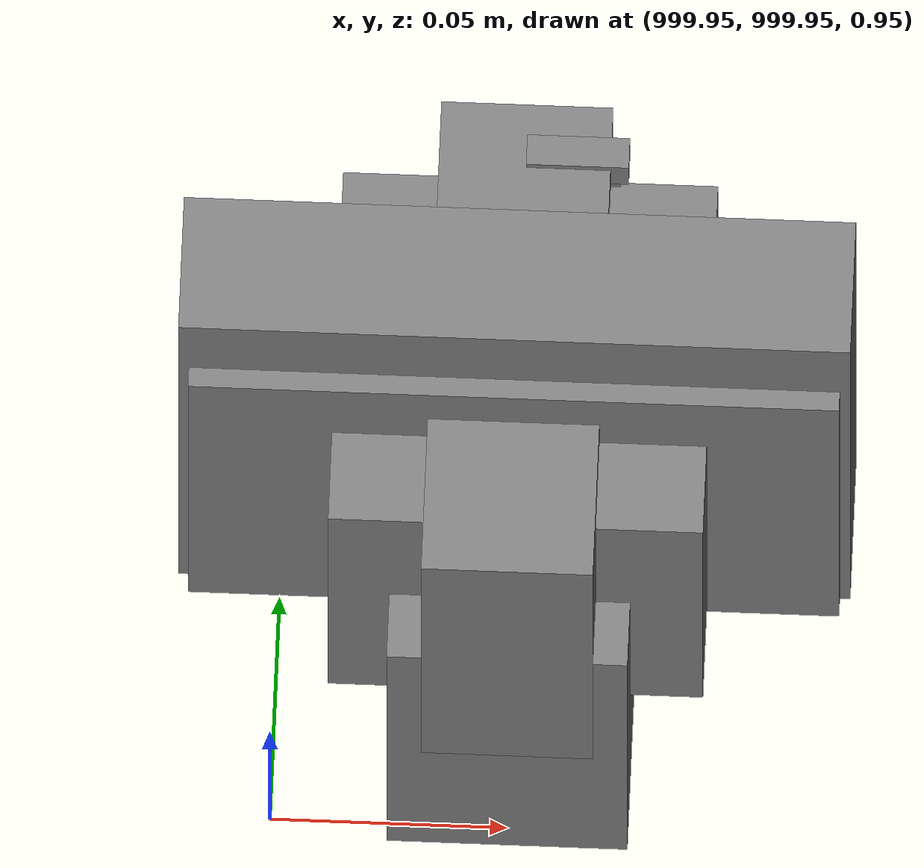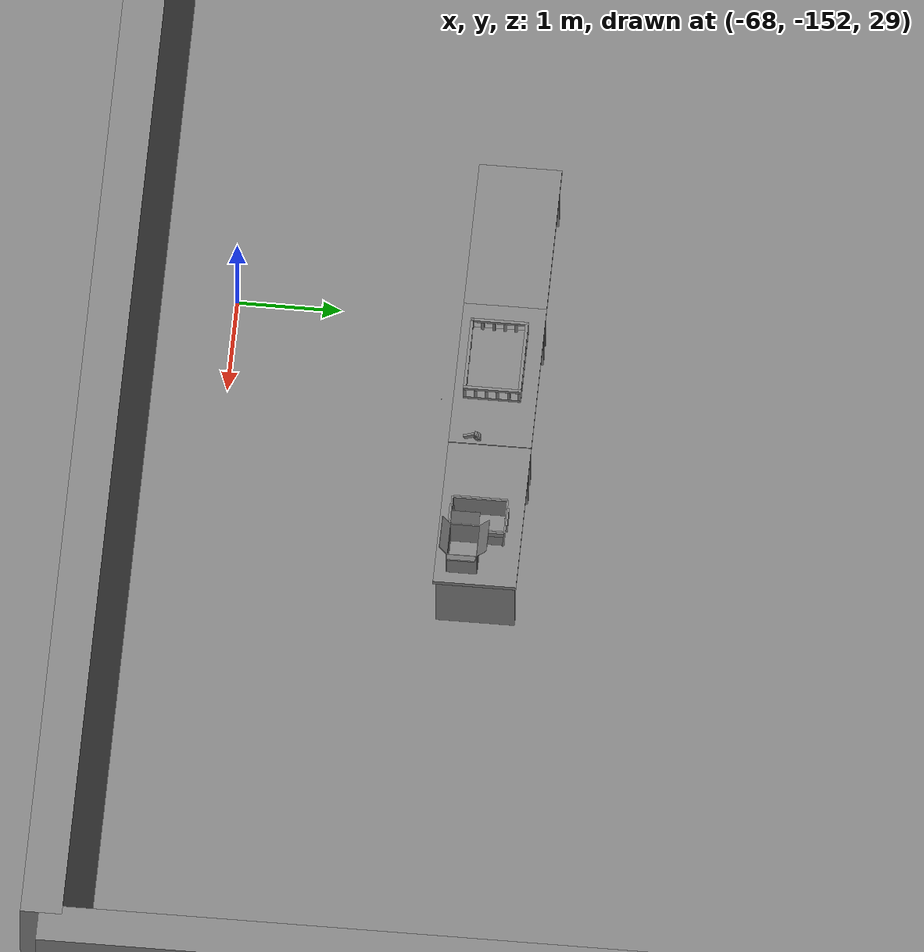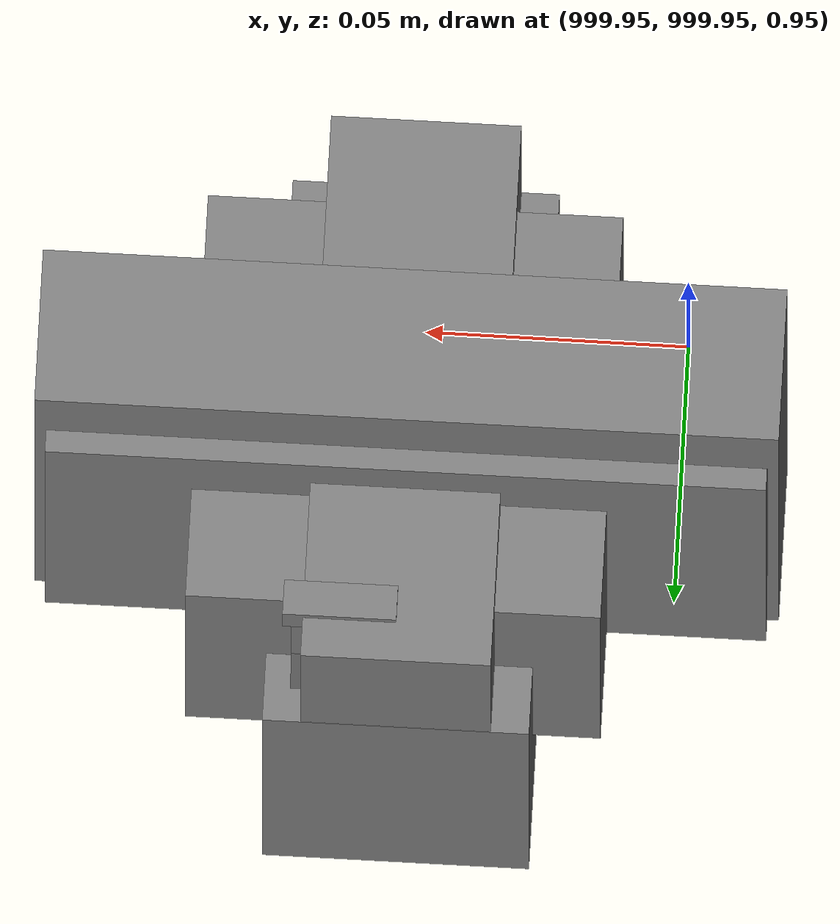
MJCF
<mujoco>
    <option gravity="0.000000000 0.000000000 -9.810000420" timestep="0.0049999999" integrator="implicitfast" density="1.225" viscosity="1.8000001e-05" noslip_iterations="10" iterations="100" sdf_iterations="50">
        <flag multiccd="disable"/>
    </option>
    <size memory="1000M"/>
    <compiler coordinate="local"/>
    <worldbody>
        <light cutoff="30" pos="0 1 1" dir="0 -1 -2"/>
        <light cutoff="30" pos="0 -1 1" dir="0 1 -2"/>
        <body pos="1000.000000000 1000.000000000 1.000000000" euler="0.000000000 0.000000000 180.000000000" name="openloong_gripper_2f85_fix_base_usda_cpu_fan">
            <geom contype="1" conaffinity="1" density="1000" type="box" material="" rgba="0.500000000 0.500000000 0.500000000 1.000000000" solimp="0.899999976 0.949999988 0.001000000" friction="1.000000000 0.005000000 0.000100000" solref="0.020000000 1.000000000" margin="0" condim="3" group="0" pos="0.000000000 0.000000000 0.070034981" quat="0.000000000 0.000000000 0.000000000 1.000000000" size="0.070700005 0.014699999 0.070700005" name="openloong_gripper_2f85_fix_base_usda_geom_04ABFD4A_BC5A_4E54_857C_66530511FAC0"/>
            <freejoint name="openloong_gripper_2f85_fix_base_usda_cpu_fan_joint"/>
            <site size="0.005000000 0.005000000 0.005000000" rgba="0.500000000 0.500000000 0.500000000 1.000000000" pos="0.000000000 0.000000000 0.000000000" quat="0.999961913 0.008726535 0.000000000 0.000000000" group="0" type="sphere" name="openloong_gripper_2f85_fix_base_usda_cpu_fancsite"/>
        </body>
        <body pos="1000.000000000 1000.000000000 1.000000000" euler="0.000000000 0.000000000 180.000000000" name="openloong_gripper_2f85_fix_base_usda_wifi_box">
            <geom contype="1" conaffinity="1" density="1000" type="box" material="" rgba="0.500000000 0.500000000 0.500000000 1.000000000" solimp="0.899999976 0.949999988 0.001000000" friction="1.000000000 0.005000000 0.000100000" solref="0.020000000 1.000000000" margin="0" condim="3" group="0" pos="0.000000000 0.000000000 0.058978677" quat="0.000000000 0.000000047 0.000000000 1.000000000" size="0.068499997 0.018999999 0.059000000" name="openloong_gripper_2f85_fix_base_usda_geom_88C785E3_DE1F_460A_9112_DF94464A38AC"/>
            <freejoint name="openloong_gripper_2f85_fix_base_usda_wifi_box_joint"/>
            <site size="0.005000000 0.005000000 0.005000000" rgba="0.500000000 0.500000000 0.500000000 1.000000000" pos="0.000000000 0.000000000 0.000000000" quat="0.999961913 0.008726500 0.000000000 0.000000000" group="0" type="sphere" name="openloong_gripper_2f85_fix_base_usda_wifi_boxsite"/>
        </body>
        <body pos="-66.392547607 -149.576217651 31.166170120" euler="-36.171161652 81.078727722 -26.250930786" mocap="true" name="spotlight6_SpotLight"/>
        <body pos="1000.000000000 999.999938965 1.000000000" euler="0.000000000 0.000000000 180.000000000" name="openloong_gripper_2f85_fix_base_usda_intelcore_i5">
            <geom contype="1" conaffinity="1" density="1000" type="box" material="" rgba="0.500000000 0.500000000 0.500000000 1.000000000" solimp="0.899999976 0.949999988 0.001000000" friction="1.000000000 0.005000000 0.000100000" solref="0.020000000 1.000000000" margin="0" condim="3" group="0" pos="0.000000000 0.000000000 0.051722717" quat="0.707106709 0.000000000 0.000000000 -0.707106769" size="0.052800000 0.018080002 0.052800000" name="openloong_gripper_2f85_fix_base_usda_geom_BED71FB1_C888_480C_A7C9_11F84E2D7C35"/>
            <freejoint name="openloong_gripper_2f85_fix_base_usda_intelcore_i5_joint"/>
            <site size="0.005000000 0.005000000 0.005000000" rgba="0.500000000 0.500000000 0.500000000 1.000000000" pos="0.000000000 0.000000000 0.000000000" quat="0.999961913 0.008726534 0.000000000 0.000000000" group="0" type="sphere" name="openloong_gripper_2f85_fix_base_usda_intelcore_i5site"/>
        </body>
        <body pos="1000.000000000 1000.000000000 1.000000000" euler="0.000011953 0.000005123 -179.999984741" name="openloong_gripper_2f85_fix_base_usda_intel_box">
            <geom contype="1" conaffinity="1" density="1000" type="box" material="" rgba="0.500000000 0.500000000 0.500000000 1.000000000" solimp="0.899999976 0.949999988 0.001000000" friction="1.000000000 0.005000000 0.000100000" solref="0.020000000 1.000000000" margin="0" condim="3" group="0" pos="0.000000000 -0.000067139 0.000082284" quat="0.707106709 0.000000225 0.000000253 0.707106650" size="0.052800003 0.025300000 0.052800003" name="openloong_gripper_2f85_fix_base_usda_geom_6243CC74_8031_4017_B551_62A539DAA268"/>
            <freejoint name="openloong_gripper_2f85_fix_base_usda_intel_box_joint"/>
            <site size="0.005000000 0.005000000 0.005000000" rgba="0.500000000 0.500000000 0.500000000 1.000000000" pos="0.000000000 0.000000000 0.000000000" quat="0.999961913 0.008726500 0.000000000 0.000000000" group="0" type="sphere" name="openloong_gripper_2f85_fix_base_usda_intel_boxsite"/>
        </body>
        <body pos="-65.802322388 -149.737060547 31.167942047" euler="-154.709594727 -34.205493927 -167.902069092" mocap="true" name="spotlight3_SpotLight"/>
        <body pos="-66.236900330 -148.927825928 31.171926498" euler="94.161796570 43.012638092 -140.534667969" mocap="true" name="spotlight2_SpotLight"/>
        <body pos="1000.000000000 1000.000000000 1.000000000" euler="0.000000000 0.000000000 180.000000000" name="openloong_gripper_2f85_fix_base_usda_battery_01">
            <geom contype="1" conaffinity="1" density="1000" type="box" material="" rgba="0.500000000 0.500000000 0.500000000 1.000000000" solimp="0.899999976 0.949999988 0.001000000" friction="1.000000000 0.005000000 0.000100000" solref="0.020000000 1.000000000" margin="0" condim="3" group="0" pos="-0.011123657 -0.041940309 0.101691343" quat="1.000000000 0.000000000 0.000000000 0.000000000" size="0.010800000 0.003375000 0.004725000" name="openloong_gripper_2f85_fix_base_usda_geom_A1DB021C_1AED_4631_A229_890DE3D51F30"/>
            <geom contype="1" conaffinity="1" density="1000" type="box" material="" rgba="0.500000000 0.500000000 0.500000000 1.000000000" solimp="0.899999976 0.949999988 0.001000000" friction="1.000000000 0.005000000 0.000100000" solref="0.020000000 1.000000000" margin="0" condim="3" group="0" pos="-0.010876465 -0.044247437 0.047066893" quat="0.998702705 -0.050920475 0.000000000 0.000000000" size="0.009450001 0.002700000 0.024975000" name="openloong_gripper_2f85_fix_base_usda_geom_AFF8BD18_ABA4_464B_A633_A756F2F8CBCE"/>
            <geom contype="1" conaffinity="1" density="1000" type="box" material="" rgba="0.500000000 0.500000000 0.500000000 1.000000000" solimp="0.899999976 0.949999988 0.001000000" friction="1.000000000 0.005000000 0.000100000" solref="0.020000000 1.000000000" margin="0" condim="3" group="0" pos="-0.001235962 -0.000659180 0.047381196" quat="1.000000000 0.000000000 0.000000000 0.000000000" size="0.039420001 0.039150000 0.047250003" name="openloong_gripper_2f85_fix_base_usda_geom_59FDF27E_1A6B_4B45_87A8_1E50518D11E1"/>
            <geom contype="1" conaffinity="1" density="1000" type="box" material="" rgba="0.500000000 0.500000000 0.500000000 1.000000000" solimp="0.899999976 0.949999988 0.001000000" friction="1.000000000 0.005000000 0.000100000" solref="0.020000000 1.000000000" margin="0" condim="3" group="0" pos="-0.010876465 -0.039138794 0.009851727" quat="1.000000000 0.000000000 0.000000000 0.000000000" size="0.009450001 0.010800000 0.013500000" name="openloong_gripper_2f85_fix_base_usda_geom_903E5233_1F96_4F58_B276_18B9E11A659F"/>
            <geom contype="1" conaffinity="1" density="1000" type="box" material="" rgba="0.500000000 0.500000000 0.500000000 1.000000000" solimp="0.899999976 0.949999988 0.001000000" friction="1.000000000 0.005000000 0.000100000" solref="0.020000000 1.000000000" margin="0" condim="3" group="0" pos="-0.010876465 -0.041528322 0.071508206" quat="1.000000000 0.000000000 0.000000000 0.000000000" size="0.009450001 0.002700000 0.027000001" name="openloong_gripper_2f85_fix_base_usda_geom_DE5A6540_714B_44D2_A24D_B28B5842288C"/>
            <freejoint name="openloong_gripper_2f85_fix_base_usda_battery_01_joint"/>
            <site size="0.005000000 0.005000000 0.005000000" rgba="0.500000000 0.500000000 0.500000000 1.000000000" pos="0.000000000 0.000000000 0.000000000" quat="0.999961913 0.008726500 0.000000000 0.000000000" group="0" type="sphere" name="openloong_gripper_2f85_fix_base_usda_battery_01site"/>
        </body>
        <body pos="-64.866622925 -149.383972168 30.183746338" euler="89.999984741 89.999946594 0.000000000" name="openloong_gripper_2f85_fix_base_usda_bluebox_01">
            <geom contype="1" conaffinity="1" density="1000" type="box" material="" rgba="0.500000000 0.500000000 0.500000000 1.000000000" solimp="0.899999976 0.949999988 0.001000000" friction="1.000000000 0.005000000 0.000100000" solref="0.020000000 1.000000000" margin="0" condim="3" group="0" pos="0.276580811 0.187225342 0.000068665" quat="0.707106948 0.000077471 0.707106352 0.000077486" size="0.100000001 0.057999998 0.010000000" name="openloong_gripper_2f85_fix_base_usda_geom_B7F50CAD_A168_4CDA_A190_88943511956C"/>
            <geom contype="1" conaffinity="1" density="1000" type="box" material="" rgba="0.500000000 0.500000000 0.500000000 1.000000000" solimp="0.899999976 0.949999988 0.001000000" friction="1.000000000 0.005000000 0.000100000" solref="0.020000000 1.000000000" margin="0" condim="3" group="0" pos="0.000000000 0.002883911 0.000000000" quat="0.999999881 0.000000000 0.000000000 0.000000000" size="0.254000008 0.003000000 0.172000006" name="openloong_gripper_2f85_fix_base_usda_geom_8EE51E95_2104_44C8_9A87_3BF1D098B0A6"/>
            <geom contype="1" conaffinity="1" density="1000" type="box" material="" rgba="0.500000000 0.500000000 0.500000000 1.000000000" solimp="0.899999976 0.949999988 0.001000000" friction="1.000000000 0.005000000 0.000100000" solref="0.020000000 1.000000000" margin="0" condim="3" group="0" pos="0.000000000 0.124874115 0.173484802" quat="0.999796331 0.020176515 -0.000000015 0.000000030" size="0.259999990 0.119999997 0.007000000" name="openloong_gripper_2f85_fix_base_usda_geom_FE89CE81_4971_4FAE_8683_F51FEDF1E9CC"/>
            <geom contype="1" conaffinity="1" density="1000" type="box" material="" rgba="0.500000000 0.500000000 0.500000000 1.000000000" solimp="0.899999976 0.949999988 0.001000000" friction="1.000000000 0.005000000 0.000100000" solref="0.020000000 1.000000000" margin="0" condim="3" group="0" pos="0.000000000 0.124874115 -0.173469543" quat="0.999796331 -0.020176545 -0.000000015 0.000000000" size="0.259999990 0.119999997 0.007000000" name="openloong_gripper_2f85_fix_base_usda_geom_5893DF90_4F96_4A91_A904_AFBDCFA0C639"/>
            <geom contype="1" conaffinity="1" density="1000" type="box" material="" rgba="0.500000000 0.500000000 0.500000000 1.000000000" solimp="0.899999976 0.949999988 0.001000000" friction="1.000000000 0.005000000 0.000100000" solref="0.020000000 1.000000000" margin="0" condim="3" group="0" pos="0.000000000 0.214008331 0.188980103" quat="0.999912977 0.013176724 0.000000015 0.000000000" size="0.259999990 0.029999999 0.012500000" name="openloong_gripper_2f85_fix_base_usda_geom_ABEA219E_5D43_4EC4_BAD7_E5FDE63C6545"/>
            <geom contype="1" conaffinity="1" density="1000" type="box" material="" rgba="0.500000000 0.500000000 0.500000000 1.000000000" solimp="0.899999976 0.949999988 0.001000000" friction="1.000000000 0.005000000 0.000100000" solref="0.020000000 1.000000000" margin="0" condim="3" group="0" pos="-0.258361816 0.125289917 0.001876831" quat="0.702796936 -0.020792112 0.710783124 0.020769298" size="0.189999998 0.119999997 0.009000000" name="openloong_gripper_2f85_fix_base_usda_geom_2102F185_7A76_4F86_A0F3_3DCF88C1F48B"/>
            <geom contype="1" conaffinity="1" density="1000" type="box" material="" rgba="0.500000000 0.500000000 0.500000000 1.000000000" solimp="0.899999976 0.949999988 0.001000000" friction="1.000000000 0.005000000 0.000100000" solref="0.020000000 1.000000000" margin="0" condim="3" group="0" pos="0.000000000 0.214008331 -0.188980103" quat="0.999912977 -0.013176769 0.000000030 0.000000015" size="0.259999990 0.029999999 0.012500000" name="openloong_gripper_2f85_fix_base_usda_geom_5DB4A1C9_ADF4_4FBC_B90F_4B6406ADED1A"/>
            <geom contype="1" conaffinity="1" density="1000" type="box" material="" rgba="0.500000000 0.500000000 0.500000000 1.000000000" solimp="0.899999976 0.949999988 0.001000000" friction="1.000000000 0.005000000 0.000100000" solref="0.020000000 1.000000000" margin="0" condim="3" group="0" pos="-0.276611328 0.187225342 0.000068665" quat="0.707106650 0.000077441 0.707106709 0.000077456" size="0.100000001 0.057999998 0.010000000" name="openloong_gripper_2f85_fix_base_usda_geom_E85DCED7_2F52_4F83_9CD1_01639F4E3E01"/>
            <geom contype="1" conaffinity="1" density="1000" type="box" material="" rgba="0.500000000 0.500000000 0.500000000 1.000000000" solimp="0.899999976 0.949999988 0.001000000" friction="1.000000000 0.005000000 0.000100000" solref="0.020000000 1.000000000" margin="0" condim="3" group="0" pos="0.258331299 0.125289917 0.001876831" quat="0.702851415 0.018856421 0.710823774 -0.019329369" size="0.189999998 0.119999997 0.009000000" name="openloong_gripper_2f85_fix_base_usda_geom_E032BEE6_7180_4DC3_9D71_F68E55613936"/>
            <freejoint name="openloong_gripper_2f85_fix_base_usda_bluebox_01_joint"/>
            <site size="0.005000000 0.005000000 0.005000000" rgba="0.500000000 0.500000000 0.500000000 1.000000000" pos="0.000000000 0.000000000 0.000000000" quat="0.999961913 0.008726534 0.000000000 0.000000000" group="0" type="sphere" name="openloong_gripper_2f85_fix_base_usda_bluebox_01site"/>
        </body>
        <body pos="-64.496299744 -149.491867065 30.235729218" euler="0.000000000 0.000000000 89.999946594" name="openloong_gripper_2f85_fix_base_usda_cardboardbox_01">
            <geom contype="1" conaffinity="1" density="1000" type="box" material="" rgba="0.500000000 0.500000000 0.500000000 1.000000000" solimp="0.899999976 0.949999988 0.001000000" friction="1.000000000 0.005000000 0.000100000" solref="0.020000000 1.000000000" margin="0" condim="3" group="0" pos="-0.003166199 -0.004086494 0.005052090" quat="1.000000000 0.000000000 0.000000000 0.000000000" size="0.142499998 0.177500010 0.005000000" name="openloong_gripper_2f85_fix_base_usda_geom_DCD9959C_7585_4191_8AC7_7E06BC2451ED"/>
            <geom contype="1" conaffinity="1" density="1000" type="box" material="" rgba="0.500000000 0.500000000 0.500000000 1.000000000" solimp="0.899999976 0.949999988 0.001000000" friction="1.000000000 0.005000000 0.000100000" solref="0.020000000 1.000000000" margin="0" condim="3" group="0" pos="-0.003166199 0.170316696 0.150570869" quat="1.000000000 0.000000000 0.000000000 0.000000000" size="0.142499998 0.005000000 0.149999991" name="openloong_gripper_2f85_fix_base_usda_geom_1343534D_6C5F_4E4D_80AF_E6AE0E94D53D"/>
            <geom contype="1" conaffinity="1" density="1000" type="box" material="" rgba="0.500000000 0.500000000 0.500000000 1.000000000" solimp="0.899999976 0.949999988 0.001000000" friction="1.000000000 0.005000000 0.000100000" solref="0.020000000 1.000000000" margin="0" condim="3" group="0" pos="-0.147399902 -0.005307198 0.150570869" quat="1.000000000 0.000000000 0.000000000 0.000000000" size="0.005000000 0.177500010 0.149999991" name="openloong_gripper_2f85_fix_base_usda_geom_86332442_DB36_4316_9418_FFB3986E5E60"/>
            <geom contype="1" conaffinity="1" density="1000" type="box" material="" rgba="0.500000000 0.500000000 0.500000000 1.000000000" solimp="0.899999976 0.949999988 0.001000000" friction="1.000000000 0.005000000 0.000100000" solref="0.020000000 1.000000000" margin="0" condim="3" group="0" pos="0.140275955 -0.005307198 0.150570869" quat="1.000000000 0.000000000 0.000000000 0.000000000" size="0.005000000 0.177500010 0.149999991" name="openloong_gripper_2f85_fix_base_usda_geom_E83F0ED4_C57B_478C_B55C_658EC7129BCD"/>
            <geom contype="1" conaffinity="1" density="1000" type="box" material="" rgba="0.500000000 0.500000000 0.500000000 1.000000000" solimp="0.899999976 0.949999988 0.001000000" friction="1.000000000 0.005000000 0.000100000" solref="0.020000000 1.000000000" margin="0" condim="3" group="0" pos="-0.003166199 -0.181550980 0.150570869" quat="1.000000000 0.000000000 0.000000000 0.000000000" size="0.142499998 0.005000000 0.149999991" name="openloong_gripper_2f85_fix_base_usda_geom_53C6F210_2E1D_4AD9_B0CC_2888DF637EA4"/>
            <freejoint name="openloong_gripper_2f85_fix_base_usda_cardboardbox_01_joint"/>
            <site size="0.005000000 0.005000000 0.005000000" rgba="0.500000000 0.500000000 0.500000000 1.000000000" pos="0.000000000 0.000000000 0.000000000" quat="0.999961913 0.008726535 0.000000000 0.000000000" group="0" type="sphere" name="openloong_gripper_2f85_fix_base_usda_site_B01D9B26_A16E_47C8_93D4_CAF71851DE05"/>
            <body pos="0.139160156 -0.004048347 0.301930904" euler="-179.999954224 49.383502960 179.999954224" name="openloong_gripper_2f85_fix_base_usda_A1_006">
                <geom contype="1" conaffinity="1" density="1000" type="box" material="" rgba="0.500000000 0.500000000 0.500000000 1.000000000" solimp="0.899999976 0.949999988 0.001000000" friction="1.000000000 0.005000000 0.000100000" solref="0.020000000 1.000000000" margin="0" condim="3" group="0" pos="-0.071587563 0.000009537 0.001745224" quat="0.999999881 0.000000000 0.000000000 0.000000000" size="0.071249999 0.179999992 0.002500000" name="openloong_gripper_2f85_fix_base_usda_geom_10BF2051_EFFC_41D0_9E28_A61F98A3244A"/>
                <joint armature="0" stiffness="0.07" damping="0.0099999998" axis="0.000000 1.000000 0.000000" type="hinge" name="openloong_gripper_2f85_fix_base_usda_A1_006"/>
            </body>
            <body pos="-0.145902634 -0.004086494 0.301938057" euler="-180.000000000 -60.000011444 -180.000000000" name="openloong_gripper_2f85_fix_base_usda_A2_006">
                <geom contype="1" conaffinity="1" density="1000" type="box" material="" rgba="0.500000000 0.500000000 0.500000000 1.000000000" solimp="0.899999976 0.949999988 0.001000000" friction="1.000000000 0.005000000 0.000100000" solref="0.020000000 1.000000000" margin="0" condim="3" group="0" pos="0.071268082 0.000009537 0.002717972" quat="0.000002921 0.000000000 -0.000000030 0.999999881" size="0.071249999 0.179999992 0.002500000" name="openloong_gripper_2f85_fix_base_usda_geom_055FFE14_F723_4342_9A46_79670D9053FF"/>
                <joint armature="0" stiffness="0.07" damping="0.0099999998" axis="0.000000 1.000000 0.000000" type="hinge" name="openloong_gripper_2f85_fix_base_usda_A2_006"/>
            </body>
            <body pos="-0.003385544 0.175991058 0.301930904" euler="-125.858116150 -0.000004561 0.000002331" name="openloong_gripper_2f85_fix_base_usda_B2_006">
                <geom contype="1" conaffinity="1" density="1000" type="box" material="" rgba="0.500000000 0.500000000 0.500000000 1.000000000" solimp="0.899999976 0.949999988 0.001000000" friction="1.000000000 0.005000000 0.000100000" solref="0.020000000 1.000000000" margin="0" condim="3" group="0" pos="0.000009537 -0.070939064 -0.002470016" quat="0.999614120 0.027776197 -0.000000015 0.000000030" size="0.137500003 0.064999998 0.005000000" name="openloong_gripper_2f85_fix_base_usda_geom_4C62675E_E6F9_42C5_8F53_26AA1669C46A"/>
                <joint armature="0" stiffness="0.07" damping="0.0099999998" axis="1.000000 0.000000 0.000000" type="hinge" name="openloong_gripper_2f85_fix_base_usda_B2_006"/>
            </body>
            <body pos="-0.003385544 -0.184140205 0.301938057" euler="147.805557251 0.000000000 0.000000000" name="openloong_gripper_2f85_fix_base_usda_B1_006">
                <geom contype="1" conaffinity="1" density="1000" type="box" material="" rgba="0.500000000 0.500000000 0.500000000 1.000000000" solimp="0.899999976 0.949999988 0.001000000" friction="1.000000000 0.005000000 0.000100000" solref="0.020000000 1.000000000" margin="0" condim="3" group="0" pos="-0.000028610 0.070202351 -0.002703667" quat="0.999614179 -0.027776167 0.000000000 0.000000000" size="0.137500003 0.064999998 0.005000000" name="openloong_gripper_2f85_fix_base_usda_geom_596B6594_4AA9_44B5_9AFB_E3F81BE1B7C6"/>
                <joint armature="0" stiffness="0.07" damping="0.0099999998" axis="1.000000 0.000000 0.000000" type="hinge" name="openloong_gripper_2f85_fix_base_usda_B1_006"/>
            </body>
        </body>
        <body pos="-65.882858276 -149.481979370 30.229999542" euler="-64.487716675 0.000000000 0.000000000" name="openloong_gripper_2f85_fix_base_usda_Barcode">
            <geom contype="1" conaffinity="1" density="1000" type="box" material="" rgba="0.500000000 0.500000000 0.500000000 1.000000000" solimp="0.899999976 0.949999988 0.001000000" friction="1.000000000 0.005000000 0.000100000" solref="0.020000000 1.000000000" margin="0" condim="3" group="0" pos="0.000000000 0.013038635 0.001419067" quat="0.000000000 0.000000000 0.000000000 1.000000119" size="0.034000002 0.010000000 0.017999999" name="openloong_gripper_2f85_fix_base_usda_geom_EDE68337_4651_4284_A76F_74BBA238284C"/>
            <geom contype="1" conaffinity="1" density="1000" type="box" material="" rgba="0.500000000 0.500000000 0.500000000 1.000000000" solimp="0.899999976 0.949999988 0.001000000" friction="1.000000000 0.005000000 0.000100000" solref="0.020000000 1.000000000" margin="0" condim="3" group="0" pos="0.000000000 -0.035301208 -0.007095337" quat="0.000000000 0.000000000 -0.043619365 0.999048233" size="0.028999999 0.010000000 0.020000000" name="openloong_gripper_2f85_fix_base_usda_geom_0911734C_398C_495C_9825_7BFFAD3914EC"/>
            <geom contype="1" conaffinity="1" density="1000" type="box" material="" rgba="0.500000000 0.500000000 0.500000000 1.000000000" solimp="0.899999976 0.949999988 0.001000000" friction="1.000000000 0.005000000 0.000100000" solref="0.020000000 1.000000000" margin="0" condim="3" group="0" pos="0.000000000 -0.043411255 -0.011749268" quat="0.922262907 0.386563420 0.000000000 0.000000000" size="0.026000001 0.010000000 0.020000000" name="openloong_gripper_2f85_fix_base_usda_geom_A3F37EB9_F537_4369_B12E_A5CC3EAF5262"/>
            <geom contype="1" conaffinity="1" density="1000" type="box" material="" rgba="0.500000000 0.500000000 0.500000000 1.000000000" solimp="0.899999976 0.949999988 0.001000000" friction="1.000000000 0.005000000 0.000100000" solref="0.020000000 1.000000000" margin="0" condim="3" group="0" pos="0.000000000 -0.016967773 -0.031860352" quat="0.000000000 0.000000000 0.000000000 1.000000119" size="0.008000000 0.010000000 0.013000000" name="openloong_gripper_2f85_fix_base_usda_geom_4ED710C6_CB94_4F8D_928D_A8FC32E85167"/>
            <geom contype="1" conaffinity="1" density="1000" type="box" material="" rgba="0.500000000 0.500000000 0.500000000 1.000000000" solimp="0.899999976 0.949999988 0.001000000" friction="1.000000000 0.005000000 0.000100000" solref="0.020000000 1.000000000" margin="0" condim="3" group="0" pos="0.000000000 -0.001869202 0.000312805" quat="0.953716993 0.300705761 0.000000000 0.000000000" size="0.032000002 0.010000000 0.018999999" name="openloong_gripper_2f85_fix_base_usda_geom_A06D3C78_3514_4FA3_B603_6DF7E44D70C1"/>
            <geom contype="1" conaffinity="1" density="1000" type="box" material="" rgba="0.500000000 0.500000000 0.500000000 1.000000000" solimp="0.899999976 0.949999988 0.001000000" friction="1.000000000 0.005000000 0.000100000" solref="0.020000000 1.000000000" margin="0" condim="3" group="0" pos="0.000000000 -0.019531250 -0.003173828" quat="0.953716993 0.300705761 0.000000000 0.000000000" size="0.030999999 0.010000000 0.020000000" name="openloong_gripper_2f85_fix_base_usda_geom_CB13A45D_81E9_422A_AA2B_EE32130FA7FE"/>
            <geom contype="1" conaffinity="1" density="1000" type="box" material="" rgba="0.500000000 0.500000000 0.500000000 1.000000000" solimp="0.899999976 0.949999988 0.001000000" friction="1.000000000 0.005000000 0.000100000" solref="0.020000000 1.000000000" margin="0" condim="3" group="0" pos="0.000000000 -0.035301208 -0.007095337" quat="0.953716993 0.300705761 0.000000000 0.000000000" size="0.028999999 0.010000000 0.020000000" name="openloong_gripper_2f85_fix_base_usda_geom_E00865D4_4D69_4DAA_A621_23CEBF62760B"/>
            <geom contype="1" conaffinity="1" density="1000" type="box" material="" rgba="0.500000000 0.500000000 0.500000000 1.000000000" solimp="0.899999976 0.949999988 0.001000000" friction="1.000000000 0.005000000 0.000100000" solref="0.020000000 1.000000000" margin="0" condim="3" group="0" pos="0.000000000 -0.042617798 -0.071121216" quat="0.000000000 0.000000000 0.000000000 1.000000119" size="0.013000000 0.021000000 0.059999999" name="openloong_gripper_2f85_fix_base_usda_geom_11CBAC4D_83A2_4CF9_9458_539DD2F15DDB"/>
            <freejoint name="openloong_gripper_2f85_fix_base_usda_Barcode_joint"/>
            <site size="0.005000000 0.005000000 0.005000000" rgba="0.500000000 0.500000000 0.500000000 1.000000000" pos="0.000000000 0.000000000 0.000000000" quat="1.000000000 0.000000000 0.000000000 0.000000000" group="0" type="sphere" name="openloong_gripper_2f85_fix_base_usda_Barcode_site"/>
        </body>
        <body pos="-66.745018005 -149.392349243 30.184000015" euler="0.000000000 0.000000000 89.999946594" name="[22330815570062]_Basket_01">
            <geom contype="1" conaffinity="1" density="1000" type="box" material="" rgba="0.500000000 0.500000000 0.500000000 1.000000000" solimp="0.899999976 0.949999988 0.001000000" friction="1.000000000 0.005000000 0.000100000" solref="0.020000000 1.000000000" margin="0" condim="3" group="0" pos="-0.052425385 0.389207840 0.089787483" quat="0.707107008 0.000000000 0.000000000 0.707106411" size="0.014249999 0.014249999 0.059999999" name="[22330815570062]_geom_AC876B2D_DAA5_4F67_8DA7_5F8799E568B5"/>
            <geom contype="1" conaffinity="1" density="1000" type="box" material="" rgba="0.500000000 0.500000000 0.500000000 1.000000000" solimp="0.899999976 0.949999988 0.001000000" friction="1.000000000 0.005000000 0.000100000" solref="0.020000000 1.000000000" margin="0" condim="3" group="0" pos="0.264015198 -0.133043289 0.089787483" quat="0.707107008 0.000000000 0.000000000 0.707106411" size="0.014249999 0.014249999 0.059999999" name="[22330815570062]_geom_0FB45787_D49C_4045_BF79_64EE11BB38CF"/>
            <geom contype="1" conaffinity="1" density="1000" type="box" material="" rgba="0.500000000 0.500000000 0.500000000 1.000000000" solimp="0.899999976 0.949999988 0.001000000" friction="1.000000000 0.005000000 0.000100000" solref="0.020000000 1.000000000" margin="0" condim="3" group="0" pos="-0.264015198 -0.265548706 0.089793205" quat="0.707107008 0.000000000 0.000000000 0.707106411" size="0.014249999 0.014249999 0.059999999" name="[22330815570062]_geom_A1ABFB3D_E098_46F3_BA24_333F3A1B0149"/>
            <geom contype="1" conaffinity="1" density="1000" type="box" material="" rgba="0.500000000 0.500000000 0.500000000 1.000000000" solimp="0.899999976 0.949999988 0.001000000" friction="1.000000000 0.005000000 0.000100000" solref="0.020000000 1.000000000" margin="0" condim="3" group="0" pos="-0.160263062 -0.389322281 0.089793205" quat="0.707107008 0.000000000 0.000000000 0.707106411" size="0.014249999 0.014249999 0.059999999" name="[22330815570062]_geom_179EEBF9_DB89_4B88_8AD0_25854C4F4756"/>
            <geom contype="1" conaffinity="1" density="1000" type="box" material="" rgba="0.500000000 0.500000000 0.500000000 1.000000000" solimp="0.899999976 0.949999988 0.001000000" friction="1.000000000 0.005000000 0.000100000" solref="0.020000000 1.000000000" margin="0" condim="3" group="0" pos="0.162265778 -0.389322281 0.089787483" quat="0.707107008 0.000000000 0.000000000 0.707106411" size="0.014249999 0.014249999 0.059999999" name="[22330815570062]_geom_F39F0429_65BB_4993_A0DD_9A649BFC63CF"/>
            <geom contype="1" conaffinity="1" density="1000" type="box" material="" rgba="0.500000000 0.500000000 0.500000000 1.000000000" solimp="0.899999976 0.949999988 0.001000000" friction="1.000000000 0.005000000 0.000100000" solref="0.020000000 1.000000000" margin="0" condim="3" group="0" pos="0.264015198 0.389207840 0.089787483" quat="0.707107008 0.000000000 0.000000000 0.707106411" size="0.014249999 0.014249999 0.059999999" name="[22330815570062]_geom_80788106_ED1A_4F5C_A20E_769358122004"/>
            <geom contype="1" conaffinity="1" density="1000" type="box" material="" rgba="0.500000000 0.500000000 0.500000000 1.000000000" solimp="0.899999976 0.949999988 0.001000000" friction="1.000000000 0.005000000 0.000100000" solref="0.020000000 1.000000000" margin="0" condim="3" group="0" pos="-0.264015198 -0.133043289 0.089793205" quat="0.707107008 0.000000000 0.000000000 0.707106411" size="0.014249999 0.014249999 0.059999999" name="[22330815570062]_geom_573DBA46_77C3_47F0_8ABD_CDD445B883A1"/>
            <geom contype="1" conaffinity="1" density="1000" type="box" material="" rgba="0.500000000 0.500000000 0.500000000 1.000000000" solimp="0.899999976 0.949999988 0.001000000" friction="1.000000000 0.005000000 0.000100000" solref="0.020000000 1.000000000" margin="0" condim="3" group="0" pos="-0.264026642 0.269256592 0.089793205" quat="0.707107008 0.000000000 0.000000000 0.707106411" size="0.014249999 0.014249999 0.059999999" name="[22330815570062]_geom_1C655029_778F_47CC_9912_AD15337D1679"/>
            <geom contype="1" conaffinity="1" density="1000" type="box" material="" rgba="0.500000000 0.500000000 0.500000000 1.000000000" solimp="0.899999976 0.949999988 0.001000000" friction="1.000000000 0.005000000 0.000100000" solref="0.020000000 1.000000000" margin="0" condim="3" group="0" pos="0.054462433 0.389207840 0.089787483" quat="0.707107008 0.000000000 0.000000000 0.707106411" size="0.014249999 0.014249999 0.059999999" name="[22330815570062]_geom_DC59D5AA_CD06_4FE2_BC12_BC0D56EA0D79"/>
            <geom contype="1" conaffinity="1" density="1000" type="box" material="" rgba="0.500000000 0.500000000 0.500000000 1.000000000" solimp="0.899999976 0.949999988 0.001000000" friction="1.000000000 0.005000000 0.000100000" solref="0.020000000 1.000000000" margin="0" condim="3" group="0" pos="0.054462433 -0.389322281 0.089787483" quat="0.707107008 0.000000000 0.000000000 0.707106411" size="0.014249999 0.014249999 0.059999999" name="[22330815570062]_geom_AA055BD0_EBD1_4CF7_B48A_E60990966685"/>
            <geom contype="1" conaffinity="1" density="1000" type="box" material="" rgba="0.500000000 0.500000000 0.500000000 1.000000000" solimp="0.899999976 0.949999988 0.001000000" friction="1.000000000 0.005000000 0.000100000" solref="0.020000000 1.000000000" margin="0" condim="3" group="0" pos="0.264015198 0.269256592 0.089793205" quat="0.707107008 0.000000000 0.000000000 0.707106411" size="0.014249999 0.014249999 0.059999999" name="[22330815570062]_geom_353AFC46_10DD_4600_A539_48A446B661AD"/>
            <geom contype="1" conaffinity="1" density="1000" type="box" material="" rgba="0.500000000 0.500000000 0.500000000 1.000000000" solimp="0.899999976 0.949999988 0.001000000" friction="1.000000000 0.005000000 0.000100000" solref="0.020000000 1.000000000" margin="0" condim="3" group="0" pos="0.264015198 -0.389322281 0.089787483" quat="0.707107008 0.000000000 0.000000000 0.707106411" size="0.014249999 0.014249999 0.059999999" name="[22330815570062]_geom_6990BF42_E065_41D2_9637_323394DADFB7"/>
            <geom contype="1" conaffinity="1" density="1000" type="box" material="" rgba="0.500000000 0.500000000 0.500000000 1.000000000" solimp="0.899999976 0.949999988 0.001000000" friction="1.000000000 0.005000000 0.000100000" solref="0.020000000 1.000000000" margin="0" condim="3" group="0" pos="0.000000000 0.000000000 0.015998840" quat="0.707107008 0.000000000 0.000000000 0.707106411" size="0.403499991 0.279000014 0.015750000" name="[22330815570062]_geom_F1A87CF0_C9E0_44B8_817C_65F64BD81503"/>
            <geom contype="1" conaffinity="1" density="1000" type="box" material="" rgba="0.500000000 0.500000000 0.500000000 1.000000000" solimp="0.899999976 0.949999988 0.001000000" friction="1.000000000 0.005000000 0.000100000" solref="0.020000000 1.000000000" margin="0" condim="3" group="0" pos="0.000000000 -0.389476776 0.163619041" quat="0.707107008 0.000000000 0.000000000 0.707106411" size="0.015000000 0.277500004 0.015750000" name="[22330815570062]_geom_C71A3E78_FECA_44BD_A141_FD777820FF5C"/>
            <geom contype="1" conaffinity="1" density="1000" type="box" material="" rgba="0.500000000 0.500000000 0.500000000 1.000000000" solimp="0.899999976 0.949999988 0.001000000" friction="1.000000000 0.005000000 0.000100000" solref="0.020000000 1.000000000" margin="0" condim="3" group="0" pos="0.162265778 0.389207840 0.089787483" quat="0.707107008 0.000000000 0.000000000 0.707106411" size="0.014249999 0.014249999 0.059999999" name="[22330815570062]_geom_2011D9ED_C2C9_4E4A_AF6D_A5C592A446E0"/>
            <geom contype="1" conaffinity="1" density="1000" type="box" material="" rgba="0.500000000 0.500000000 0.500000000 1.000000000" solimp="0.899999976 0.949999988 0.001000000" friction="1.000000000 0.005000000 0.000100000" solref="0.020000000 1.000000000" margin="0" condim="3" group="0" pos="0.000000000 0.389471054 0.163619041" quat="0.707107008 0.000000000 0.000000000 0.707106411" size="0.015000000 0.277500004 0.015750000" name="[22330815570062]_geom_081081C3_34F8_4C89_B622_052B29AC2B1F"/>
            <geom contype="1" conaffinity="1" density="1000" type="box" material="" rgba="0.500000000 0.500000000 0.500000000 1.000000000" solimp="0.899999976 0.949999988 0.001000000" friction="1.000000000 0.005000000 0.000100000" solref="0.020000000 1.000000000" margin="0" condim="3" group="0" pos="-0.263511658 0.000000000 0.163619041" quat="0.707107008 0.000000000 0.000000000 0.707106411" size="0.403499991 0.015000000 0.015750000" name="[22330815570062]_geom_DE34BADA_E730_49F8_B014_854DD51EC50B"/>
            <geom contype="1" conaffinity="1" density="1000" type="box" material="" rgba="0.500000000 0.500000000 0.500000000 1.000000000" solimp="0.899999976 0.949999988 0.001000000" friction="1.000000000 0.005000000 0.000100000" solref="0.020000000 1.000000000" margin="0" condim="3" group="0" pos="-0.264015198 0.141334534 0.089793205" quat="0.707107008 0.000000000 0.000000000 0.707106411" size="0.014249999 0.014249999 0.059999999" name="[22330815570062]_geom_84C0965E_77FF_48C9_BD57_ECCDA6F85F71"/>
            <geom contype="1" conaffinity="1" density="1000" type="box" material="" rgba="0.500000000 0.500000000 0.500000000 1.000000000" solimp="0.899999976 0.949999988 0.001000000" friction="1.000000000 0.005000000 0.000100000" solref="0.020000000 1.000000000" margin="0" condim="3" group="0" pos="0.264015198 -0.265548706 0.089787483" quat="0.707107008 0.000000000 0.000000000 0.707106411" size="0.014249999 0.014249999 0.059999999" name="[22330815570062]_geom_D55A43B1_7D6E_4965_833B_DAEE0F9DEC4C"/>
            <geom contype="1" conaffinity="1" density="1000" type="box" material="" rgba="0.500000000 0.500000000 0.500000000 1.000000000" solimp="0.899999976 0.949999988 0.001000000" friction="1.000000000 0.005000000 0.000100000" solref="0.020000000 1.000000000" margin="0" condim="3" group="0" pos="-0.160263062 0.389207840 0.089787483" quat="0.707107008 0.000000000 0.000000000 0.707106411" size="0.014249999 0.014249999 0.059999999" name="[22330815570062]_geom_25506891_ABD5_4CD2_97CB_80CF598AC086"/>
            <geom contype="1" conaffinity="1" density="1000" type="box" material="" rgba="0.500000000 0.500000000 0.500000000 1.000000000" solimp="0.899999976 0.949999988 0.001000000" friction="1.000000000 0.005000000 0.000100000" solref="0.020000000 1.000000000" margin="0" condim="3" group="0" pos="-0.052425385 -0.389322281 0.089787483" quat="0.707107008 0.000000000 0.000000000 0.707106411" size="0.014249999 0.014249999 0.059999999" name="[22330815570062]_geom_F021516B_7CA3_4921_9A8B_EB7586C9ABBA"/>
            <geom contype="1" conaffinity="1" density="1000" type="box" material="" rgba="0.500000000 0.500000000 0.500000000 1.000000000" solimp="0.899999976 0.949999988 0.001000000" friction="1.000000000 0.005000000 0.000100000" solref="0.020000000 1.000000000" margin="0" condim="3" group="0" pos="-0.264026642 -0.389322281 0.089793205" quat="0.707107008 0.000000000 0.000000000 0.707106411" size="0.014249999 0.014249999 0.059999999" name="[22330815570062]_geom_B2013438_1944_4753_AB26_9AAB7B2B41F2"/>
            <geom contype="1" conaffinity="1" density="1000" type="box" material="" rgba="0.500000000 0.500000000 0.500000000 1.000000000" solimp="0.899999976 0.949999988 0.001000000" friction="1.000000000 0.005000000 0.000100000" solref="0.020000000 1.000000000" margin="0" condim="3" group="0" pos="0.264015198 0.141334534 0.089787483" quat="0.707107008 0.000000000 0.000000000 0.707106411" size="0.014249999 0.014249999 0.059999999" name="[22330815570062]_geom_D632A178_083A_4A94_926A_FD031CD7FC1F"/>
            <geom contype="1" conaffinity="1" density="1000" type="box" material="" rgba="0.500000000 0.500000000 0.500000000 1.000000000" solimp="0.899999976 0.949999988 0.001000000" friction="1.000000000 0.005000000 0.000100000" solref="0.020000000 1.000000000" margin="0" condim="3" group="0" pos="-0.264015198 0.389207840 0.089793205" quat="0.707107008 0.000000000 0.000000000 0.707106411" size="0.014249999 0.014249999 0.059999999" name="[22330815570062]_geom_AB35B861_209A_4B6F_8A8B_532B8C23D88C"/>
            <geom contype="1" conaffinity="1" density="1000" type="box" material="" rgba="0.500000000 0.500000000 0.500000000 1.000000000" solimp="0.899999976 0.949999988 0.001000000" friction="1.000000000 0.005000000 0.000100000" solref="0.020000000 1.000000000" margin="0" condim="3" group="0" pos="0.264015198 0.004480362 0.089787483" quat="0.707107008 0.000000000 0.000000000 0.707106411" size="0.014249999 0.014249999 0.059999999" name="[22330815570062]_geom_4328158B_60E6_46DD_BBB7_0A0900352B85"/>
            <geom contype="1" conaffinity="1" density="1000" type="box" material="" rgba="0.500000000 0.500000000 0.500000000 1.000000000" solimp="0.899999976 0.949999988 0.001000000" friction="1.000000000 0.005000000 0.000100000" solref="0.020000000 1.000000000" margin="0" condim="3" group="0" pos="0.263694763 -0.000011444 0.163619041" quat="0.707107008 0.000000000 0.000000000 0.707106411" size="0.403499991 0.015000000 0.015750000" name="[22330815570062]_geom_BD66AC30_3405_457C_B521_53CA3F3BCD9F"/>
            <geom contype="1" conaffinity="1" density="1000" type="box" material="" rgba="0.500000000 0.500000000 0.500000000 1.000000000" solimp="0.899999976 0.949999988 0.001000000" friction="1.000000000 0.005000000 0.000100000" solref="0.020000000 1.000000000" margin="0" condim="3" group="0" pos="-0.264015198 0.004480362 0.089793205" quat="0.707107008 0.000000000 0.000000000 0.707106411" size="0.014249999 0.014249999 0.059999999" name="[22330815570062]_geom_577693EA_B790_4127_99A1_EEA5185D5668"/>
            <freejoint name="[22330815570062]_joint_36BE4E6F_AED9_4194_AFE1_60DF095C906E"/>
        </body>
        <body pos="0.000000000 0.000000000 0.000000000" euler="0.000000000 0.000000000 0.000000000" name="Static Objects_Static Objects">
            <geom contype="1" conaffinity="1" density="1000" type="box" material="" rgba="0.500000000 0.500000000 0.500000000 1.000000000" solimp="0.899999976 0.949999988 0.001000000" friction="1.000000000 0.005000000 0.000100000" solref="0.020000000 1.000000000" margin="0" condim="3" group="0" pos="-67.544113159 -149.365814209 29.727830887" quat="0.500000417 0.499999970 0.499999553 0.499999970" size="0.381000012 0.319999993 0.041000001" name="Static Objects_geom_720AE354_914F_45C8_A011_4DB3F14C694A"/>
            <geom contype="1" conaffinity="1" density="1000" type="box" material="" rgba="0.500000000 0.500000000 0.500000000 1.000000000" solimp="0.899999976 0.949999988 0.001000000" friction="1.000000000 0.005000000 0.000100000" solref="0.020000000 1.000000000" margin="0" condim="3" group="0" pos="-68.239501953 -149.365814209 30.086868286" quat="0.500000417 0.499999970 0.499999553 0.499999970" size="0.370999992 0.039500002 0.745000005" name="Static Objects_geom_24A66332_9124_4284_A271_922B9C06B58E"/>
            <geom contype="1" conaffinity="1" density="1000" type="box" material="" rgba="0.500000000 0.500000000 0.500000000 1.000000000" solimp="0.899999976 0.949999988 0.001000000" friction="1.000000000 0.005000000 0.000100000" solref="0.020000000 1.000000000" margin="0" condim="3" group="0" pos="-68.239501953 -149.365814209 30.147235870" quat="0.500000417 0.499999970 0.499999553 0.499999970" size="0.400000006 0.022000000 0.800000012" name="Static Objects_geom_43CAC060_E5F3_416B_8FEC_A9D193E44249"/>
            <geom contype="1" conaffinity="1" density="1000" type="box" material="" rgba="0.500000000 0.500000000 0.500000000 1.000000000" solimp="0.899999976 0.949999988 0.001000000" friction="1.000000000 0.005000000 0.000100000" solref="0.020000000 1.000000000" margin="0" condim="3" group="0" pos="-68.934890747 -149.365814209 29.727830887" quat="0.500000417 0.499999970 0.499999553 0.499999970" size="0.381000012 0.319999993 0.041000001" name="Static Objects_geom_86DDEB0A_98EE_4DEF_AEE7_22DBC2D561E5"/>
            <geom contype="1" conaffinity="1" density="1000" type="box" material="" rgba="0.500000000 0.500000000 0.500000000 1.000000000" solimp="0.899999976 0.949999988 0.001000000" friction="1.000000000 0.005000000 0.000100000" solref="0.020000000 1.000000000" margin="0" condim="3" group="0" pos="-68.239501953 -149.365814209 29.561563492" quat="0.500000417 0.499999970 0.499999553 0.499999970" size="0.020000000 0.022000000 0.660000026" name="Static Objects_geom_5C217701_8DD6_4025_BD6E_7915875D9494"/>
            <geom contype="1" conaffinity="1" density="1000" type="box" material="" rgba="0.500000000 0.500000000 0.500000000 1.000000000" solimp="0.899999976 0.949999988 0.001000000" friction="1.000000000 0.005000000 0.000100000" solref="0.020000000 1.000000000" margin="0" condim="3" group="0" pos="-65.945671082 -149.365814209 29.727830887" quat="0.500000417 0.499999970 0.499999553 0.499999970" size="0.381000012 0.319999993 0.041000001" name="Static Objects_geom_7E6B2DED_AEE7_44ED_9218_3E46A9B35ED5"/>
            <geom contype="1" conaffinity="1" density="1000" type="box" material="" rgba="0.500000000 0.500000000 0.500000000 1.000000000" solimp="0.899999976 0.949999988 0.001000000" friction="1.000000000 0.005000000 0.000100000" solref="0.020000000 1.000000000" margin="0" condim="3" group="0" pos="-66.641059875 -149.365814209 30.086868286" quat="0.500000417 0.499999970 0.499999553 0.499999970" size="0.370999992 0.039500002 0.745000005" name="Static Objects_geom_95782661_568F_43EB_8932_E8580A1BA412"/>
            <geom contype="1" conaffinity="1" density="1000" type="box" material="" rgba="0.500000000 0.500000000 0.500000000 1.000000000" solimp="0.899999976 0.949999988 0.001000000" friction="1.000000000 0.005000000 0.000100000" solref="0.020000000 1.000000000" margin="0" condim="3" group="0" pos="-66.641059875 -149.365814209 30.147235870" quat="0.500000417 0.499999970 0.499999553 0.499999970" size="0.400000006 0.022000000 0.800000012" name="Static Objects_geom_46B6CBAA_C2E8_40CB_9D64_9F596BD3B059"/>
            <geom contype="1" conaffinity="1" density="1000" type="box" material="" rgba="0.500000000 0.500000000 0.500000000 1.000000000" solimp="0.899999976 0.949999988 0.001000000" friction="1.000000000 0.005000000 0.000100000" solref="0.020000000 1.000000000" margin="0" condim="3" group="0" pos="-67.336448669 -149.365814209 29.727830887" quat="0.500000417 0.499999970 0.499999553 0.499999970" size="0.381000012 0.319999993 0.041000001" name="Static Objects_geom_7F9702D4_B649_4B82_B483_85071E52108B"/>
            <geom contype="1" conaffinity="1" density="1000" type="box" material="" rgba="0.500000000 0.500000000 0.500000000 1.000000000" solimp="0.899999976 0.949999988 0.001000000" friction="1.000000000 0.005000000 0.000100000" solref="0.020000000 1.000000000" margin="0" condim="3" group="0" pos="-66.641059875 -149.365814209 29.561563492" quat="0.500000417 0.499999970 0.499999553 0.499999970" size="0.020000000 0.022000000 0.660000026" name="Static Objects_geom_A175F131_A17D_4DBC_9604_D4F50E8A9269"/>
            <geom contype="1" conaffinity="1" density="1000" type="box" material="" rgba="0.500000000 0.500000000 0.500000000 1.000000000" solimp="0.899999976 0.949999988 0.001000000" friction="1.000000000 0.005000000 0.000100000" solref="0.020000000 1.000000000" margin="0" condim="3" group="0" pos="-64.338577271 -149.365814209 29.727830887" quat="0.500000417 0.499999970 0.499999553 0.499999970" size="0.381000012 0.319999993 0.041000001" name="Static Objects_geom_B0488A45_B3B8_47E8_A7E0_E1623FC264DD"/>
            <geom contype="1" conaffinity="1" density="1000" type="box" material="" rgba="0.500000000 0.500000000 0.500000000 1.000000000" solimp="0.899999976 0.949999988 0.001000000" friction="1.000000000 0.005000000 0.000100000" solref="0.020000000 1.000000000" margin="0" condim="3" group="0" pos="-65.033966064 -149.365814209 30.086868286" quat="0.500000417 0.499999970 0.499999553 0.499999970" size="0.370999992 0.039500002 0.745000005" name="Static Objects_geom_3FA47295_BCC2_4689_A6C8_09A7063F65B7"/>
            <geom contype="1" conaffinity="1" density="1000" type="box" material="" rgba="0.500000000 0.500000000 0.500000000 1.000000000" solimp="0.899999976 0.949999988 0.001000000" friction="1.000000000 0.005000000 0.000100000" solref="0.020000000 1.000000000" margin="0" condim="3" group="0" pos="-65.033966064 -149.365814209 30.147235870" quat="0.500000417 0.499999970 0.499999553 0.499999970" size="0.400000006 0.022000000 0.800000012" name="Static Objects_geom_9F593E82_EE9D_4278_81DA_8069C1700668"/>
            <geom contype="1" conaffinity="1" density="1000" type="box" material="" rgba="0.500000000 0.500000000 0.500000000 1.000000000" solimp="0.899999976 0.949999988 0.001000000" friction="1.000000000 0.005000000 0.000100000" solref="0.020000000 1.000000000" margin="0" condim="3" group="0" pos="-65.729354858 -149.365814209 29.727830887" quat="0.500000417 0.499999970 0.499999553 0.499999970" size="0.381000012 0.319999993 0.041000001" name="Static Objects_geom_D0D7BCFA_CE43_442F_9DD1_28E780E4E6E7"/>
            <geom contype="1" conaffinity="1" density="1000" type="box" material="" rgba="0.500000000 0.500000000 0.500000000 1.000000000" solimp="0.899999976 0.949999988 0.001000000" friction="1.000000000 0.005000000 0.000100000" solref="0.020000000 1.000000000" margin="0" condim="3" group="0" pos="-65.033966064 -149.365814209 29.561563492" quat="0.500000417 0.499999970 0.499999553 0.499999970" size="0.020000000 0.022000000 0.660000026" name="Static Objects_geom_65F90F8B_6C32_43A2_84C1_8A466A863E5A"/>
            <geom contype="1" conaffinity="1" density="1000" type="box" material="" rgba="0.500000000 0.500000000 0.500000000 1.000000000" solimp="0.899999976 0.949999988 0.001000000" friction="1.000000000 0.005000000 0.000100000" solref="0.020000000 1.000000000" margin="0" condim="3" group="0" pos="-61.754566193 -137.853729248 33.906845093" quat="0.707107067 0.000000000 0.000000000 0.707106471" size="0.759999990 0.759999990 4.500000000" name="Static Objects_geom_D6DC3C0E_FD04_4F60_8473_F3DD7B0DC345"/>
            <geom contype="1" conaffinity="1" density="1000" type="box" material="" rgba="0.500000000 0.500000000 0.500000000 1.000000000" solimp="0.899999976 0.949999988 0.001000000" friction="1.000000000 0.005000000 0.000100000" solref="0.020000000 1.000000000" margin="0" condim="3" group="0" pos="-57.511135101 -144.927108765 31.707921982" quat="1.000000000 0.000000000 0.000000000 0.000000000" size="0.200000003 8.000000000 2.299999952" name="Static Objects_geom_97C47F83_671C_45BE_83BF_BA000A7BA9D3"/>
            <geom contype="1" conaffinity="1" density="1000" type="box" material="" rgba="0.500000000 0.500000000 0.500000000 1.000000000" solimp="0.899999976 0.949999988 0.001000000" friction="1.000000000 0.005000000 0.000100000" solref="0.020000000 1.000000000" margin="0" condim="3" group="0" pos="-80.517646790 -157.574050903 31.688196182" quat="0.707107067 0.000000000 0.000000000 0.707106471" size="0.600000024 0.600000024 2.299999952" name="Static Objects_geom_61EB4D16_1962_4EB9_9FA1_8B24EA676079"/>
            <geom contype="1" conaffinity="1" density="1000" type="box" material="" rgba="0.500000000 0.500000000 0.500000000 1.000000000" solimp="0.899999976 0.949999988 0.001000000" friction="1.000000000 0.005000000 0.000100000" solref="0.020000000 1.000000000" margin="0" condim="3" group="0" pos="-80.711044312 -147.414932251 31.666158676" quat="1.000000000 0.000000000 0.000000000 0.000000000" size="0.200000003 10.000000000 2.299999952" name="Static Objects_geom_22711413_1D41_49D9_9C80_5E336839BCA0"/>
            <geom contype="1" conaffinity="1" density="1000" type="box" material="" rgba="0.500000000 0.500000000 0.500000000 1.000000000" solimp="0.899999976 0.949999988 0.001000000" friction="1.000000000 0.005000000 0.000100000" solref="0.020000000 1.000000000" margin="0" condim="3" group="0" pos="-57.687217712 -137.434692383 31.688196182" quat="0.707107067 0.000000000 0.000000000 0.707106471" size="0.600000024 0.600000024 2.299999952" name="Static Objects_geom_B4BF5BD2_D90F_4BC3_B8E0_F50FF0B2CAA4"/>
            <geom contype="1" conaffinity="1" density="1000" type="box" material="" rgba="0.500000000 0.500000000 0.500000000 1.000000000" solimp="0.899999976 0.949999988 0.001000000" friction="1.000000000 0.005000000 0.000100000" solref="0.020000000 1.000000000" margin="0" condim="3" group="0" pos="-69.537033081 -140.263229370 31.714921951" quat="0.707107067 0.000000000 0.000000000 0.707106471" size="0.759999990 4.500000000 2.299999952" name="Static Objects_geom_8745742B_2C1D_43EF_AF7B_FF48EADB9850"/>
            <geom contype="1" conaffinity="1" density="1000" type="box" material="" rgba="0.500000000 0.500000000 0.500000000 1.000000000" solimp="0.899999976 0.949999988 0.001000000" friction="1.000000000 0.005000000 0.000100000" solref="0.020000000 1.000000000" margin="0" condim="3" group="0" pos="-80.073638916 -137.853713989 33.906845093" quat="0.707107067 0.000000000 0.000000000 0.707106471" size="0.759999990 0.759999990 4.500000000" name="Static Objects_geom_65EC2BD3_850F_49ED_872A_2A9B9405DA66"/>
            <geom contype="1" conaffinity="1" density="1000" type="box" material="" rgba="0.500000000 0.500000000 0.500000000 1.000000000" solimp="0.899999976 0.949999988 0.001000000" friction="1.000000000 0.005000000 0.000100000" solref="0.020000000 1.000000000" margin="0" condim="3" group="0" pos="-73.406707764 -155.734664917 31.707921982" quat="1.000000000 0.000000000 0.000000000 0.000000000" size="0.200000003 3.000000000 2.299999952" name="Static Objects_geom_83E3AD68_6CA9_4FA5_A098_24959F88D46F"/>
            <geom contype="1" conaffinity="1" density="1000" type="box" material="" rgba="0.500000000 0.500000000 0.500000000 1.000000000" solimp="0.899999976 0.949999988 0.001000000" friction="1.000000000 0.005000000 0.000100000" solref="0.020000000 1.000000000" margin="0" condim="3" group="0" pos="-68.497543335 -137.448257446 31.707921982" quat="0.707107067 0.000000000 0.000000000 0.707106471" size="0.200000003 14.000000000 2.299999952" name="Static Objects_geom_085FBCA6_C23F_4696_BC35_56B893DD06EE"/>
            <geom contype="1" conaffinity="1" density="1000" type="cylinder" material="" rgba="0.500000000 0.500000000 0.500000000 1.000000000" solimp="0.899999976 0.949999988 0.001000000" friction="1.000000000 0.005000000 0.000100000" solref="0.020000000 1.000000000" margin="0" condim="3" group="0" pos="-68.868522644 -142.134506226 31.711090088" quat="0.707107067 0.000000000 0.000000000 0.707106471" size="0.509999990 2.299999952 1.000000000" name="Static Objects_geom_2B252DF5_7D61_4422_8953_5AACE3435916"/>
            <geom contype="1" conaffinity="1" density="1000" type="plane" material="" rgba="0.500000000 0.500000000 0.500000000 1.000000000" solimp="0.899999976 0.949999988 0.001000000" friction="1.000000000 0.005000000 0.000100000" solref="0.020000000 1.000000000" margin="0" condim="3" group="0" pos="-72.873703003 -147.131927490 29.409669876" quat="1.000000000 0.000000000 0.000000000 0.000000000" size="18.000000000 14.000000000 1.000000000" name="Static Objects_geom_44518D44_77A5_4872_B676_1209362983EF"/>
            <geom contype="1" conaffinity="1" density="1000" type="box" material="" rgba="0.500000000 0.500000000 0.500000000 1.000000000" solimp="0.899999976 0.949999988 0.001000000" friction="1.000000000 0.005000000 0.000100000" solref="0.020000000 1.000000000" margin="0" condim="3" group="0" pos="-79.943580627 -157.782272339 31.707921982" quat="0.707107067 0.000000000 0.000000000 0.707106471" size="0.200000003 7.000000000 2.299999952" name="Static Objects_geom_A4F53946_D5F6_4067_ACC8_1E32B25AE1A6"/>
            <geom contype="1" conaffinity="1" density="1000" type="box" material="" rgba="0.500000000 0.500000000 0.500000000 1.000000000" solimp="0.899999976 0.949999988 0.001000000" friction="1.000000000 0.005000000 0.000100000" solref="0.020000000 1.000000000" margin="0" condim="3" group="0" pos="-65.421028137 -152.903442383 31.707921982" quat="0.707107067 0.000000000 0.000000000 0.707106471" size="0.200000003 7.800000191 2.299999952" name="Static Objects_geom_37729528_9987_4F09_9BE3_9D3B7629B6C2"/>
            <geom contype="1" conaffinity="1" density="1000" type="box" material="" rgba="0.500000000 0.500000000 0.500000000 1.000000000" solimp="0.899999976 0.949999988 0.001000000" friction="1.000000000 0.005000000 0.000100000" solref="0.020000000 1.000000000" margin="0" condim="3" group="0" pos="-74.776908875 -149.964416504 31.688196182" quat="1.000000000 0.000000000 0.000000000 0.000000000" size="0.600000024 0.409999996 2.299999952" name="Static Objects_geom_FB6FD21E_0E9A_4B9B_A5F6_A2A7AB8B2C38"/>
            <geom contype="1" conaffinity="1" density="1000" type="cylinder" material="" rgba="0.500000000 0.500000000 0.500000000 1.000000000" solimp="0.899999976 0.949999988 0.001000000" friction="1.000000000 0.005000000 0.000100000" solref="0.020000000 1.000000000" margin="0" condim="3" group="0" pos="-60.161884308 -142.134506226 31.711090088" quat="0.707107067 0.000000000 0.000000000 0.707106471" size="0.509999990 2.299999952 1.000000000" name="Static Objects_geom_0FC9F248_F283_447E_A61D_2C9684E4BC82"/>
            <geom contype="1" conaffinity="1" density="1000" type="cylinder" material="" rgba="0.500000000 0.500000000 0.500000000 1.000000000" solimp="0.899999976 0.949999988 0.001000000" friction="1.000000000 0.005000000 0.000100000" solref="0.020000000 1.000000000" margin="0" condim="3" group="0" pos="-75.382453918 -149.963455200 31.711090088" quat="0.707107067 0.000000000 0.000000000 0.707106471" size="0.409999996 2.299999952 1.000000000" name="Static Objects_geom_1C6444F3_5D5F_416A_AE5D_00027C922746"/>
            <geom contype="1" conaffinity="1" density="1000" type="cylinder" material="" rgba="0.500000000 0.500000000 0.500000000 1.000000000" solimp="0.899999976 0.949999988 0.001000000" friction="1.000000000 0.005000000 0.000100000" solref="0.020000000 1.000000000" margin="0" condim="3" group="0" pos="-74.154960632 -149.963455200 31.711090088" quat="0.707107067 0.000000000 0.000000000 0.707106471" size="0.409999996 2.299999952 1.000000000" name="Static Objects_geom_C1059BD0_D04F_4A07_ABAE_5AC31D66FD62"/>
            <geom contype="1" conaffinity="1" density="1000" type="cylinder" material="" rgba="0.500000000 0.500000000 0.500000000 1.000000000" solimp="0.899999976 0.949999988 0.001000000" friction="1.000000000 0.005000000 0.000100000" solref="0.020000000 1.000000000" margin="0" condim="3" group="0" pos="-77.566612244 -142.134506226 31.711090088" quat="0.707107067 0.000000000 0.000000000 0.707106471" size="0.509999990 2.299999952 1.000000000" name="Static Objects_geom_5EECEFE5_989B_4FF8_AF53_0C9885325959"/>
        </body>
        <body pos="-66.291030884 -149.869689941 29.018842697" euler="0.000000000 0.000000000 89.999946594" mocap="true" name="openloong_gripper_2f85_fix_base_usda_leftHandMocap"/>
        <body pos="-66.291030884 -149.869689941 29.018842697" euler="0.000000000 0.000000000 89.999946594" mocap="true" name="openloong_gripper_2f85_fix_base_usda_rightHandMocap"/>
        <body pos="-66.291030884 -149.869689941 30.218843460" euler="0.000000000 0.000000000 89.999946594" name="openloong_gripper_2f85_fix_base_usda_base_link">
            <geom contype="1" conaffinity="1" density="1000" type="mesh" material="" rgba="0.783999979 0.783999979 0.783999979 1.000000000" solimp="0.899999976 0.949999988 0.001000000" friction="1.000000000 0.005000000 0.000100000" solref="0.020000000 1.000000000" margin="0" condim="3" group="3" mesh="base_link" pos="0.000000000 0.000000000 0.000000000" quat="1.000000000 0.000000000 0.000000000 0.000000000" size="1.000000000 1.000000000 1.000000000" name="openloong_gripper_2f85_fix_base_usda__geom_7_32DAAE64_8D9E_4F45_837F_AF1E5C1CFF1B"/>
            <site size="0.005000000 0.005000000 0.005000000" rgba="0.500000000 0.500000000 0.500000000 1.000000000" pos="0.000000000 0.000000000 0.000000000" quat="1.000000000 0.000000000 0.000000000 0.000000000" group="0" type="sphere" name="openloong_gripper_2f85_fix_base_usda_imu"/>
            <inertial mass="22.447001" pos="-0.005664100 -0.001336700 0.238289997" diaginertia="0.374352545 0.277180195 0.220617250" quat="0.999247074 0.035235517 -0.015086859 0.006023135"/>
            <body pos="0.000000000 0.000000000 0.299997330" euler="0.000000000 0.000000000 0.000000000" name="openloong_gripper_2f85_fix_base_usda_dummy_body">
                <geom contype="1" conaffinity="1" density="1000" type="sphere" material="" rgba="0.783999979 0.783999979 0.783999979 1.000000000" solimp="0.899999976 0.949999988 0.001000000" friction="1.000000000 0.005000000 0.000100000" solref="0.020000000 1.000000000" margin="0" condim="3" group="3" pos="0.000000000 0.000000000 0.000000000" quat="1.000000000 0.000000000 0.000000000 0.000000000" size="0.010000000 0.000000000 0.000000000" name="openloong_gripper_2f85_fix_base_usda__geom_8_8DE30375_76D7_43D3_94C9_CF6CA382A0E9"/>
                <joint armature="0.0099999998" stiffness="0" damping="0.1" axis="0.000000 0.000000 1.000000" type="hinge" name="openloong_gripper_2f85_fix_base_usda_dummy_joint"/>
                <site size="0.010000000 0.005000000 0.005000000" rgba="0.500000000 0.500000000 0.500000000 1.000000000" pos="0.000000000 0.000000000 0.000000000" quat="1.000000000 0.000000000 0.000000000 0.000000000" group="3" type="sphere" name="openloong_gripper_2f85_fix_base_usda_dummy_site"/>
            </body>
            <body pos="0.009002686 0.000000000 0.406400681" euler="0.000000000 0.000000000 0.000000000" name="openloong_gripper_2f85_fix_base_usda_Link_head_yaw">
                <geom contype="1" conaffinity="1" density="1000" type="mesh" material="" rgba="0.783999979 0.783999979 0.783999979 1.000000000" solimp="0.899999976 0.949999988 0.001000000" friction="1.000000000 0.005000000 0.000100000" solref="0.020000000 1.000000000" margin="0" condim="3" group="3" mesh="Link_head_yaw" pos="0.000000000 0.000000000 0.000000000" quat="1.000000000 0.000000000 0.000000000 0.000000000" size="1.000000000 1.000000000 1.000000000" name="openloong_gripper_2f85_fix_base_usda__geom_10_7521479B_FB72_4ECA_9AB6_D96AD949F172"/>
                <inertial mass="0.84249002" pos="0.000000000 -0.002081400 0.044801001" diaginertia="0.000700588 0.000629000 0.000553812" quat="0.706933022 -0.015675601 0.015677100 0.706933022"/>
                <body pos="0.000000000 -0.034599304 0.048500061" euler="0.000000000 0.000000000 0.000000000" name="openloong_gripper_2f85_fix_base_usda_Link_head_pitch">
                    <geom contype="1" conaffinity="1" density="1000" type="mesh" material="" rgba="0.783999979 0.783999979 0.783999979 1.000000000" solimp="0.899999976 0.949999988 0.001000000" friction="1.000000000 0.005000000 0.000100000" solref="0.020000000 1.000000000" margin="0" condim="3" group="3" mesh="Link_head_pitch" pos="0.000000000 0.000000000 0.000000000" quat="1.000000000 0.000000000 0.000000000 0.000000000" size="1.000000000 1.000000000 1.000000000" name="openloong_gripper_2f85_fix_base_usda__geom_12_4FFD3969_943D_45C0_A497_BFB16E50D559"/>
                    <inertial mass="1.3943" pos="0.020569000 0.033004001 0.125000000" diaginertia="0.006381400 0.006289940 0.004481460" quat="0.973390222 0.008406822 0.228157058 0.019624906"/>
                    <body pos="0.000000000 0.029998779 0.000000000" euler="0.000000000 0.000000000 0.000000000" name="openloong_gripper_2f85_fix_base_usda_neck_center_body">
                        <site size="0.010000000 0.005000000 0.005000000" rgba="0.500000000 0.500000000 0.500000000 1.000000000" pos="0.000000000 0.000000000 0.000000000" quat="1.000000000 0.000000000 0.000000000 0.000000000" group="3" type="sphere" name="openloong_gripper_2f85_fix_base_usda_neck_center_site"/>
                        <body pos="0.020004272 0.000000000 0.149999619" euler="-0.000002229 39.998176575 -90.000205994" name="openloong_gripper_2f85_fix_base_usda_camera_head">
                            <site size="0.010000000 0.005000000 0.005000000" rgba="0.500000000 0.500000000 0.500000000 1.000000000" pos="0.000000000 0.000000000 0.000000000" quat="1.000000000 0.000000000 0.000000000 0.000000000" group="3" type="sphere" name="openloong_gripper_2f85_fix_base_usda_camera_head_site"/>
                        </body>
                    </body>
                </body>
            </body>
            <body pos="0.003997803 -0.161598206 0.392200470" euler="0.000000000 0.000000000 0.000000000" name="openloong_gripper_2f85_fix_base_usda_Link_arm_r_01">
                <geom contype="1" conaffinity="1" density="1000" type="mesh" material="" rgba="0.783999979 0.783999979 0.783999979 1.000000000" solimp="0.899999976 0.949999988 0.001000000" friction="1.000000000 0.005000000 0.000100000" solref="0.020000000 1.000000000" margin="0" condim="3" group="3" mesh="Link_arm_r_01" pos="0.000000000 0.000000000 0.000000000" quat="1.000000000 0.000000000 0.000000000 0.000000000" size="1.000000000 1.000000000 1.000000000" name="openloong_gripper_2f85_fix_base_usda__geom_14_7ACE1365_6123_4EC5_A749_648A5BFEC5DB"/>
                <joint armature="0.0099999998" stiffness="0" damping="1" axis="0.000000 -1.000000 0.000000" limited="true" range="-170.000015259 170.000015259" type="hinge" name="openloong_gripper_2f85_fix_base_usda_J_arm_r_01"/>
                <inertial mass="0.75641" pos="0.004494600 -0.038293999 -0.000001874" diaginertia="0.000842990 0.000803050 0.000587120" quat="-0.000163502 0.707098067 0.000812463 0.707115054"/>
                <body pos="-0.041992188 -0.041000366 0.000000000" euler="0.000000000 0.000000000 0.000000000" name="openloong_gripper_2f85_fix_base_usda_Link_arm_r_02">
                    <geom contype="1" conaffinity="1" density="1000" type="mesh" material="" rgba="0.783999979 0.783999979 0.783999979 1.000000000" solimp="0.899999976 0.949999988 0.001000000" friction="1.000000000 0.005000000 0.000100000" solref="0.020000000 1.000000000" margin="0" condim="3" group="3" mesh="Link_arm_r_02" pos="0.000000000 0.000000000 0.000000000" quat="1.000000000 0.000000000 0.000000000 0.000000000" size="1.000000000 1.000000000 1.000000000" name="openloong_gripper_2f85_fix_base_usda__geom_16_6EE47E93_6013_48AC_AE86_F188511EDDEA"/>
                    <joint armature="0.0099999998" stiffness="0" damping="1" axis="-1.000000 0.000000 0.000000" limited="true" range="-105.000244141 105.000244141" type="hinge" name="openloong_gripper_2f85_fix_base_usda_J_arm_r_02"/>
                    <inertial mass="0.98500001" pos="0.041999999 -0.067430697 0.000000000" diaginertia="0.002262690 0.001730990 0.001154020" quat="0.500000000 0.500000000 -0.500000000 0.500000000"/>
                    <body pos="0.041992188 -0.122596741 0.000000000" euler="0.000000000 0.000000000 0.000000000" name="openloong_gripper_2f85_fix_base_usda_Link_arm_r_03">
                        <geom contype="1" conaffinity="1" density="1000" type="mesh" material="" rgba="0.783999979 0.783999979 0.783999979 1.000000000" solimp="0.899999976 0.949999988 0.001000000" friction="1.000000000 0.005000000 0.000100000" solref="0.020000000 1.000000000" margin="0" condim="3" group="3" mesh="Link_arm_r_03" pos="0.000000000 0.000000000 0.000000000" quat="1.000000000 0.000000000 0.000000000 0.000000000" size="1.000000000 1.000000000 1.000000000" name="openloong_gripper_2f85_fix_base_usda__geom_18_66CEB589_F91E_4C53_BACC_F0FD0715C609"/>
                        <joint armature="0.0099999998" stiffness="0" damping="1" axis="0.000000 -1.000000 0.000000" limited="true" range="-170.000015259 170.000015259" type="hinge" name="openloong_gripper_2f85_fix_base_usda_J_arm_r_03"/>
                        <inertial mass="0.95899999" pos="-0.001413580 -0.164663002 0.020757901" diaginertia="0.002101340 0.002064590 0.000754802" quat="0.560480952 0.454391927 -0.443732947 0.531497955"/>
                        <body pos="0.035293579 -0.177406311 0.023998260" euler="0.000000000 0.000000000 0.000000000" name="openloong_gripper_2f85_fix_base_usda_Link_arm_r_04">
                            <geom contype="1" conaffinity="1" density="1000" type="mesh" material="" rgba="0.783999979 0.783999979 0.783999979 1.000000000" solimp="0.899999976 0.949999988 0.001000000" friction="1.000000000 0.005000000 0.000100000" solref="0.020000000 1.000000000" margin="0" condim="3" group="3" mesh="Link_arm_r_04" pos="0.000000000 0.000000000 0.000000000" quat="1.000000000 0.000000000 0.000000000 0.000000000" size="1.000000000 1.000000000 1.000000000" name="openloong_gripper_2f85_fix_base_usda__geom_20_0A32B31E_86DE_414E_801E_BD555435743A"/>
                            <joint armature="0.0099999998" stiffness="0" damping="1" axis="-1.000000 0.000000 0.000000" limited="true" range="0.000000000 170.000015259" type="hinge" name="openloong_gripper_2f85_fix_base_usda_J_arm_r_04"/>
                            <inertial mass="0.60000002" pos="-0.038727000 -0.060766999 -0.021003000" diaginertia="0.001092610 0.000712422 0.000645102" quat="0.327701002 0.632602990 -0.467366993 0.523443997"/>
                            <body pos="-0.035293579 -0.103492737 -0.023998260" euler="0.000000000 0.000000000 0.000000000" name="openloong_gripper_2f85_fix_base_usda_Link_arm_r_05">
                                <geom contype="1" conaffinity="1" density="1000" type="mesh" material="" rgba="0.783999979 0.783999979 0.783999979 1.000000000" solimp="0.899999976 0.949999988 0.001000000" friction="1.000000000 0.005000000 0.000100000" solref="0.020000000 1.000000000" margin="0" condim="3" group="3" mesh="Link_arm_r_05" pos="0.000000000 0.000000000 0.000000000" quat="1.000000000 0.000000000 0.000000000 0.000000000" size="1.000000000 1.000000000 1.000000000" name="openloong_gripper_2f85_fix_base_usda__geom_22_4B6AE1E6_962B_4794_80F9_7637BF017DE4"/>
                                <joint armature="0.0099999998" stiffness="0" damping="1" axis="0.000000 -1.000000 0.000000" limited="true" range="-170.000015259 170.000015259" type="hinge" name="openloong_gripper_2f85_fix_base_usda_J_arm_r_05"/>
                                <inertial mass="0.68976003" pos="0.000032712 -0.068658002 -0.000111780" diaginertia="0.002522510 0.002411100 0.000448695" quat="0.707660973 0.706543028 -0.002603360 0.002470550"/>
                                <body pos="-0.026489258 -0.196502686 0.000000000" euler="0.000000000 0.000000000 0.000000000" name="openloong_gripper_2f85_fix_base_usda_Link_arm_r_06">
                                    <geom contype="1" conaffinity="1" density="1000" type="mesh" material="" rgba="0.783999979 0.783999979 0.783999979 1.000000000" solimp="0.899999976 0.949999988 0.001000000" friction="1.000000000 0.005000000 0.000100000" solref="0.020000000 1.000000000" margin="0" condim="3" group="3" mesh="Link_arm_r_06" pos="0.000000000 0.000000000 0.000000000" quat="1.000000000 0.000000000 0.000000000 0.000000000" size="1.000000000 1.000000000 1.000000000" name="openloong_gripper_2f85_fix_base_usda__geom_24_BFB01BAC_2A52_47E3_9635_DA261BEA6AD5"/>
                                    <joint armature="0.0099999998" stiffness="0" damping="1" axis="1.000000 0.000000 0.000000" limited="true" range="-105.000244141 105.000244141" type="hinge" name="openloong_gripper_2f85_fix_base_usda_J_arm_r_06"/>
                                    <inertial mass="0.28" pos="0.026078001 -0.000000896 0.001663700" diaginertia="0.000156930 0.000145601 0.000104979" quat="0.707080841 0.001851080 0.001883810 0.707127810"/>
                                    <body pos="0.026489258 0.000000000 0.031799316" euler="0.000000000 0.000000000 0.000000000" name="openloong_gripper_2f85_fix_base_usda_Link_arm_r_07">
                                        <geom contype="1" conaffinity="1" density="1000" type="mesh" material="" rgba="0.783999979 0.783999979 0.783999979 1.000000000" solimp="0.899999976 0.949999988 0.001000000" friction="1.000000000 0.005000000 0.000100000" solref="0.020000000 1.000000000" margin="0" condim="3" group="3" mesh="Link_arm_r_07" pos="0.000000000 0.000000000 0.000000000" quat="1.000000000 0.000000000 0.000000000 0.000000000" size="1.000000000 1.000000000 1.000000000" name="openloong_gripper_2f85_fix_base_usda__geom_26_2C31ADBB_A4D4_4745_8961_0D2AB7727279"/>
                                        <joint armature="0.0099999998" stiffness="0" damping="1" axis="0.000000 0.000000 1.000000" limited="true" range="-60.000133514 60.000133514" type="hinge" name="openloong_gripper_2f85_fix_base_usda_J_arm_r_07"/>
                                        <inertial mass="0.61353999" pos="-0.007859000 -0.158170000 -0.027736001" diaginertia="0.003037610 0.002570910 0.000729379" quat="0.427542925 0.443532884 -0.553093910 0.560867906"/>
                                        <body pos="0.000000000 0.286994934 -0.270000458" euler="150.000350952 -0.000001649 -0.000000442" name="openloong_gripper_2f85_fix_base_usda_camera_wrist_r">
                                            <site size="0.010000000 0.005000000 0.005000000" rgba="0.500000000 0.500000000 0.500000000 1.000000000" pos="0.000000000 0.000000000 0.000000000" quat="1.000000000 0.000000000 0.000000000 0.000000000" group="3" type="sphere" name="openloong_gripper_2f85_fix_base_usda_camera_wrist_r_site"/>
                                        </body>
                                        <body pos="0.000000000 -0.220008850 -0.033002853" euler="0.000000000 0.000000000 179.999969482" name="openloong_gripper_2f85_fix_base_usda_ee_center_body_r">
                                            <site size="0.010000000 0.005000000 0.005000000" rgba="0.500000000 0.500000000 0.500000000 1.000000000" pos="0.000000000 0.000000000 0.000000000" quat="1.000000000 0.000000000 0.000000000 0.000000000" group="3" type="sphere" name="openloong_gripper_2f85_fix_base_usda_ee_center_site_r"/>
                                        </body>
                                        <body pos="0.000000000 -0.066001892 -0.031000137" euler="89.999984741 0.000000000 180.000000000" name="openloong_gripper_2f85_fix_base_usda_zbr_base_link">
                                            <geom contype="1" conaffinity="1" density="1000" type="mesh" material="" rgba="0.783999979 0.783999979 0.783999979 1.000000000" solimp="0.899999976 0.949999988 0.001000000" friction="1.000000000 0.005000000 0.000100000" solref="0.020000000 1.000000000" margin="0" condim="3" group="3" mesh="base" pos="0.000000000 0.000003815 -0.000007629" quat="1.000000000 0.000000000 0.000000000 0.000000000" size="1.000000238 1.000000238 1.000000238" name="openloong_gripper_2f85_fix_base_usda__geom_30_2C11942C_FF84_4E65_AF60_5E658CBB0639"/>
                                            <inertial mass="0.77744102" pos="0.000000000 -0.000027039 0.035467502" diaginertia="0.000260285 0.000225381 0.000152708" quat="0.999998808 -0.001528488 0.000000000 0.000000000"/>
                                            <body pos="-0.030609138 0.004745484 0.065696731" euler="-89.999984741 -0.000000000 0.000000000" name="openloong_gripper_2f85_fix_base_usda_r_left_driver">
                                                <geom contype="1" conaffinity="1" density="1000" type="mesh" material="" rgba="0.783999979 0.783999979 0.783999979 1.000000000" solimp="0.899999976 0.949999988 0.001000000" friction="1.000000000 0.005000000 0.000100000" solref="0.020000000 1.000000000" margin="0" condim="3" group="3" mesh="driver" pos="0.030609138 0.054901138 -0.004699708" quat="0.707106829 0.707106709 0.000000000 -0.000000000" size="1.000000238 1.000000238 1.000000238" name="openloong_gripper_2f85_fix_base_usda__geom_32_923F9F9E_4909_409B_8F1D_F793A70776AB"/>
                                                <joint armature="0.0049999999" stiffness="0" damping="0.1" axis="0.000000 0.000000 1.000000" limited="true" range="0.000000000 51.566200256" type="hinge" name="openloong_gripper_2f85_fix_base_usda_r_left_driver_joint"/>
                                                <inertial mass="0.0089956298" pos="0.000000000 0.017754700 0.001073140" diaginertia="0.000001724 0.000001609 0.000000322" quat="0.681301236 0.732003212 0.000000000 0.000000000"/>
                                                <body pos="-0.031402595 0.004524232 -0.010200503" euler="0.000000000 0.000000000 180.000000000" name="openloong_gripper_2f85_fix_base_usda_r_left_coupler">
                                                    <geom contype="1" conaffinity="1" density="1000" type="mesh" material="" rgba="0.783999979 0.783999979 0.783999979 1.000000000" solimp="0.899999976 0.949999988 0.001000000" friction="1.000000000 0.005000000 0.000100000" solref="0.020000000 1.000000000" margin="0" condim="3" group="3" mesh="coupler" pos="-0.062011734 -0.050354015 0.005500795" quat="0.707106829 -0.707106709 0.000000000 -0.000000000" size="1.000000238 1.000000238 1.000000238" name="openloong_gripper_2f85_fix_base_usda__geom_34_2BF4C1F7_F951_4724_A6E1_3E8A04660F02"/>
                                                    <inertial mass="0.0140974" pos="0.000000000 0.003012090 0.023217499" diaginertia="0.000004162 0.000003522 0.000000888" quat="0.705635548 -0.045590367 0.045590367 0.705635548"/>
                                                </body>
                                            </body>
                                            <body pos="-0.012695315 -0.012001040 0.072212234" euler="-89.999984741 -0.000000000 0.000000000" name="openloong_gripper_2f85_fix_base_usda_r_left_spring_link">
                                                <geom contype="1" conaffinity="1" density="1000" type="mesh" material="" rgba="0.783999979 0.783999979 0.783999979 1.000000000" solimp="0.899999976 0.949999988 0.001000000" friction="1.000000000 0.005000000 0.000100000" solref="0.020000000 1.000000000" margin="0" condim="3" group="3" mesh="spring_link" pos="0.012695315 0.061416641 0.012050631" quat="0.707106829 0.707106709 0.000000000 -0.000000000" size="1.000000238 1.000000238 1.000000238" name="openloong_gripper_2f85_fix_base_usda__geom_36_35636DE0_7126_4DF5_BF60_2A75E1CBB758"/>
                                                <joint armature="0.001" stiffness="0.050000001" damping="0.00125" axis="0.000000 0.000000 1.000000" limited="true" range="-17.000000000 51.566200256" type="hinge" name="openloong_gripper_2f85_fix_base_usda_r_left_spring_link_joint"/>
                                                <inertial mass="0.0221642" pos="-0.000000009 0.018162400 0.021265799" diaginertia="0.000008969 0.000006717 0.000002639" quat="0.663403213 -0.244737089 0.244737089 0.663403213"/>
                                                <body pos="-0.038208015 -0.042503368 0.002950669" euler="180.000000000 0.000000000 -0.002185660" name="openloong_gripper_2f85_fix_base_usda_r_left_follower">
                                                    <geom contype="1" conaffinity="1" density="1000" type="mesh" material="" rgba="0.783999979 0.783999979 0.783999979 1.000000000" solimp="0.899999976 0.949999988 0.001000000" friction="1.000000000 0.005000000 0.000100000" solref="0.020000000 1.000000000" margin="0" condim="3" group="3" mesh="tongue" pos="0.050918590 -0.103920005 -0.009099962" quat="0.707106829 -0.707106709 0.000000030 0.000000030" size="1.000000238 1.000000238 1.000000238" name="openloong_gripper_2f85_fix_base_usda__geom_40_FC783D33_0CFF_42B2_ADBA_843AF0063039"/>
                                                    <geom contype="1" conaffinity="1" density="1000" type="mesh" material="" rgba="0.783999979 0.783999979 0.783999979 1.000000000" solimp="0.899999976 0.949999988 0.001000000" friction="1.000000000 0.005000000 0.000100000" solref="0.020000000 1.000000000" margin="0" condim="3" group="3" mesh="follower" pos="0.050918590 -0.103920005 -0.009099962" quat="0.707106829 -0.707106709 0.000000030 0.000000030" size="1.000000238 1.000000238 1.000000238" name="openloong_gripper_2f85_fix_base_usda__geom_39_87B42777_AA8E_4BD2_AA38_0C8EB2C85118"/>
                                                    <joint armature="0.001" stiffness="0" damping="0.1" axis="0.000000 0.000000 1.000000" limited="true" range="-49.999961853 51.566200256" type="hinge" name="openloong_gripper_2f85_fix_base_usda_r_left_follower"/>
                                                    <inertial mass="0.0125222" pos="0.000000000 -0.011046000 0.012478600" diaginertia="0.000002674 0.000002456 0.000000602" quat="0.986436546 0.164143041 0.000000000 0.000000000"/>
                                                    <body pos="-0.037765510 -0.103912376 -0.009099962" euler="-89.999984741 0.000000000 0.000004829" name="openloong_gripper_2f85_fix_base_usda_r_left_pad">
                                                        <geom contype="1" conaffinity="1" density="1000" type="box" material="" rgba="0.550000012 0.550000012 0.550000012 1.000000000" solimp="0.949999988 0.990000010 0.001000000" friction="0.699999988 0.005000000 0.000100000" solref="0.020000000 1.000000000" margin="0" condim="3" group="3" mass="1e-06" pos="0.043243419 0.000003815 0.119995147" quat="0.999999881 0.000000000 0.000000000 0.000000000" size="0.002000001 0.011000003 0.009375002" name="openloong_gripper_2f85_fix_base_usda_r_left_pad1_58A66B81_8A1E_4598_901D_87129AF55290"/>
                                                        <geom contype="1" conaffinity="1" density="1000" type="box" material="" rgba="0.449999988 0.449999988 0.449999988 1.000000000" solimp="0.949999988 0.990000010 0.001000000" friction="0.600000024 0.005000000 0.000100000" solref="0.020000000 1.000000000" margin="0" condim="3" group="3" mass="1e-06" pos="0.043243419 0.000003815 0.138748199" quat="0.999999881 0.000000000 0.000000000 0.000000000" size="0.002000001 0.011000003 0.009375002" name="openloong_gripper_2f85_fix_base_usda_r_left_pad2_CFF2376D_67BD_4765_95D9_5F5BFBC126C7"/>
                                                    </body>
                                                </body>
                                            </body>
                                            <body pos="0.030593880 -0.004753114 0.065696731" euler="89.999984741 0.000000000 180.000000000" name="openloong_gripper_2f85_fix_base_usda_r_right_driver">
                                                <geom contype="1" conaffinity="1" density="1000" type="mesh" material="" rgba="0.783999979 0.783999979 0.783999979 1.000000000" solimp="0.899999976 0.949999988 0.001000000" friction="1.000000000 0.005000000 0.000100000" solref="0.020000000 1.000000000" margin="0" condim="3" group="3" mesh="driver" pos="0.030593880 0.054901138 -0.004699708" quat="0.707106829 0.707106709 0.000000000 0.000000000" size="1.000000238 1.000000238 1.000000238" name="openloong_gripper_2f85_fix_base_usda__geom_42_3597C93B_8AFC_494D_B685_6A4368D0C6CD"/>
                                                <joint armature="0.0049999999" stiffness="0" damping="0.1" axis="0.000000 0.000000 1.000000" limited="true" range="0.000000000 51.566200256" type="hinge" name="openloong_gripper_2f85_fix_base_usda_r_right_driver_joint"/>
                                                <inertial mass="0.0089956298" pos="0.000000000 0.017754700 0.001073140" diaginertia="0.000001724 0.000001609 0.000000322" quat="0.681301236 0.732003212 0.000000000 0.000000000"/>
                                                <body pos="-0.031417854 0.004531861 -0.010202411" euler="0.000000000 0.000000000 180.000000000" name="openloong_gripper_2f85_fix_base_usda_r_right_coupler">
                                                    <geom contype="1" conaffinity="1" density="1000" type="mesh" material="" rgba="0.783999979 0.783999979 0.783999979 1.000000000" solimp="0.899999976 0.949999988 0.001000000" friction="1.000000000 0.005000000 0.000100000" solref="0.020000000 1.000000000" margin="0" condim="3" group="3" mesh="coupler" pos="-0.062042251 -0.050376903 0.005500795" quat="0.707106829 -0.707106709 0.000000000 0.000000000" size="1.000000238 1.000000238 1.000000238" name="openloong_gripper_2f85_fix_base_usda__geom_44_8EC36105_667C_486B_8539_1814AFD030FA"/>
                                                    <inertial mass="0.0140974" pos="0.000000000 0.003012090 0.023217499" diaginertia="0.000004162 0.000003522 0.000000888" quat="0.705635548 -0.045590367 0.045590367 0.705635548"/>
                                                </body>
                                            </body>
                                            <body pos="0.012695315 0.011997226 0.072219864" euler="89.999984741 0.000000000 180.000000000" name="openloong_gripper_2f85_fix_base_usda_r_right_spring_link">
                                                <geom contype="1" conaffinity="1" density="1000" type="mesh" material="" rgba="0.783999979 0.783999979 0.783999979 1.000000000" solimp="0.899999976 0.949999988 0.001000000" friction="1.000000000 0.005000000 0.000100000" solref="0.020000000 1.000000000" margin="0" condim="3" group="3" mesh="spring_link" pos="0.012695315 0.061424270 0.012048724" quat="0.707106829 0.707106709 0.000000000 0.000000000" size="1.000000238 1.000000238 1.000000238" name="openloong_gripper_2f85_fix_base_usda__geom_46_5714D8C3_7D50_47B4_B1D7_EAE7DC57DAC6"/>
                                                <joint armature="0.001" stiffness="0.050000001" damping="0.00125" axis="0.000000 0.000000 1.000000" limited="true" range="-17.000000000 51.566200256" type="hinge" name="openloong_gripper_2f85_fix_base_usda_r_right_spring_link_joint"/>
                                                <inertial mass="0.0221642" pos="-0.000000009 0.018162400 0.021265799" diaginertia="0.000008969 0.000006717 0.000002639" quat="0.663403213 -0.244737089 0.244737089 0.663403213"/>
                                                <body pos="-0.038208015 -0.042495739 0.002950669" euler="180.000000000 0.000000000 0.000000000" name="openloong_gripper_2f85_fix_base_usda_r_right_follower">
                                                    <geom contype="1" conaffinity="1" density="1000" type="mesh" material="" rgba="0.783999979 0.783999979 0.783999979 1.000000000" solimp="0.899999976 0.949999988 0.001000000" friction="1.000000000 0.005000000 0.000100000" solref="0.020000000 1.000000000" margin="0" condim="3" group="3" mesh="follower" pos="0.050888073 -0.103927635 -0.009099962" quat="0.707106829 -0.707106709 0.000000000 0.000000000" size="1.000000238 1.000000238 1.000000238" name="openloong_gripper_2f85_fix_base_usda__geom_50_4F117D7E_B8AA_4785_851C_7C4CE448FDC8"/>
                                                    <geom contype="1" conaffinity="1" density="1000" type="mesh" material="" rgba="0.783999979 0.783999979 0.783999979 1.000000000" solimp="0.899999976 0.949999988 0.001000000" friction="1.000000000 0.005000000 0.000100000" solref="0.020000000 1.000000000" margin="0" condim="3" group="3" mesh="tongue" pos="0.050888073 -0.103927635 -0.009099962" quat="0.707106829 -0.707106709 0.000000000 0.000000000" size="1.000000238 1.000000238 1.000000238" name="openloong_gripper_2f85_fix_base_usda__geom_49_ED03435A_9AB9_41FC_8D7B_73BE9B998ABE"/>
                                                    <joint armature="0.001" stiffness="0" damping="0.1" axis="0.000000 0.000000 1.000000" limited="true" range="-49.999961853 51.566200256" type="hinge" name="openloong_gripper_2f85_fix_base_usda_r_right_follower_joint"/>
                                                    <inertial mass="0.0125222" pos="0.000000000 -0.011046000 0.012478600" diaginertia="0.000002674 0.000002456 0.000000602" quat="0.986436546 0.164143041 0.000000000 0.000000000"/>
                                                    <body pos="-0.037811287 -0.103927635 -0.009099962" euler="-89.999984741 0.000000000 0.000000000" name="openloong_gripper_2f85_fix_base_usda_r_right_pad">
                                                        <geom contype="1" conaffinity="1" density="1000" type="box" material="" rgba="0.449999988 0.449999988 0.449999988 1.000000000" solimp="0.949999988 0.990000010 0.001000000" friction="0.600000024 0.005000000 0.000100000" solref="0.020000000 1.000000000" margin="0" condim="3" group="3" mass="1e-06" pos="0.043258678 0.000000000 0.138748199" quat="1.000000000 0.000000000 0.000000000 0.000000000" size="0.002000001 0.011000003 0.009375002" name="openloong_gripper_2f85_fix_base_usda_r_right_pad2_D6E39C64_7F1E_4847_A501_423ABE287B86"/>
                                                        <geom contype="1" conaffinity="1" density="1000" type="box" material="" rgba="0.550000012 0.550000012 0.550000012 1.000000000" solimp="0.949999988 0.990000010 0.001000000" friction="0.699999988 0.005000000 0.000100000" solref="0.020000000 1.000000000" margin="0" condim="3" group="3" mass="1e-06" pos="0.043258678 0.000003815 0.120002776" quat="1.000000000 0.000000000 0.000000000 0.000000000" size="0.002000001 0.011000003 0.009375002" name="openloong_gripper_2f85_fix_base_usda_r_right_pad1_90DD7667_3643_456D_BFB3_213D9FD6BC7A"/>
                                                    </body>
                                                </body>
                                            </body>
                                        </body>
                                    </body>
                                </body>
                            </body>
                        </body>
                    </body>
                </body>
            </body>
            <body pos="0.003997803 0.161590576 0.392200470" euler="0.000000000 0.000000000 0.000000000" name="openloong_gripper_2f85_fix_base_usda_Link_arm_l_01">
                <geom contype="1" conaffinity="1" density="1000" type="mesh" material="" rgba="0.783999979 0.783999979 0.783999979 1.000000000" solimp="0.899999976 0.949999988 0.001000000" friction="1.000000000 0.005000000 0.000100000" solref="0.020000000 1.000000000" margin="0" condim="3" group="3" mesh="Link_arm_l_01" pos="0.000000000 0.000000000 0.000000000" quat="1.000000000 0.000000000 0.000000000 0.000000000" size="1.000000000 1.000000000 1.000000000" name="openloong_gripper_2f85_fix_base_usda__geom_52_395EDED2_BA9C_45B2_878F_A69487425F88"/>
                <joint armature="0.0099999998" stiffness="0" damping="1" axis="0.000000 1.000000 0.000000" limited="true" range="-170.000015259 170.000015259" type="hinge" name="openloong_gripper_2f85_fix_base_usda_J_arm_l_01"/>
                <inertial mass="0.75640601" pos="-0.004494650 0.038294200 -0.000001874" diaginertia="0.000842986 0.000803053 0.000587115" quat="-0.000812496 0.707115054 0.000163424 0.707098067"/>
                <body pos="0.042007446 0.041000366 0.000000000" euler="0.000000000 0.000000000 0.000000000" name="openloong_gripper_2f85_fix_base_usda_Link_arm_l_02">
                    <geom contype="1" conaffinity="1" density="1000" type="mesh" material="" rgba="0.783999979 0.783999979 0.783999979 1.000000000" solimp="0.899999976 0.949999988 0.001000000" friction="1.000000000 0.005000000 0.000100000" solref="0.020000000 1.000000000" margin="0" condim="3" group="3" mesh="Link_arm_l_02" pos="0.000000000 0.000000000 0.000000000" quat="1.000000000 0.000000000 0.000000000 0.000000000" size="1.000000000 1.000000000 1.000000000" name="openloong_gripper_2f85_fix_base_usda__geom_54_6D04ABB2_0135_4A80_B1FE_2384A6C40E33"/>
                    <joint armature="0.0099999998" stiffness="0" damping="1" axis="-1.000000 0.000000 0.000000" limited="true" range="-105.000244141 105.000244141" type="hinge" name="openloong_gripper_2f85_fix_base_usda_J_arm_l_02"/>
                    <inertial mass="0.98500001" pos="-0.041999999 0.067430697 0.000000000" diaginertia="0.002262690 0.001730990 0.001154020" quat="0.500000000 0.500000000 -0.500000000 0.500000000"/>
                    <body pos="-0.042007446 0.122596741 0.000000000" euler="0.000000000 0.000000000 0.000000000" name="openloong_gripper_2f85_fix_base_usda_Link_arm_l_03">
                        <geom contype="1" conaffinity="1" density="1000" type="mesh" material="" rgba="0.783999979 0.783999979 0.783999979 1.000000000" solimp="0.899999976 0.949999988 0.001000000" friction="1.000000000 0.005000000 0.000100000" solref="0.020000000 1.000000000" margin="0" condim="3" group="3" mesh="Link_arm_l_03" pos="0.000000000 0.000000000 0.000000000" quat="1.000000000 0.000000000 0.000000000 0.000000000" size="1.000000000 1.000000000 1.000000000" name="openloong_gripper_2f85_fix_base_usda__geom_56_241E3851_D9DC_439C_9E9B_4C92B47C6528"/>
                        <joint armature="0.0099999998" stiffness="0" damping="1" axis="0.000000 1.000000 0.000000" limited="true" range="-170.000015259 170.000015259" type="hinge" name="openloong_gripper_2f85_fix_base_usda_J_arm_l_03"/>
                        <inertial mass="0.95899999" pos="0.001413580 0.164663002 0.020757901" diaginertia="0.002101340 0.002064590 0.000754802" quat="0.443732947 0.531497955 -0.560480952 0.454391927"/>
                        <body pos="-0.035293579 0.177406311 0.023998260" euler="0.000000000 0.000000000 0.000000000" name="openloong_gripper_2f85_fix_base_usda_Link_arm_l_04">
                            <geom contype="1" conaffinity="1" density="1000" type="mesh" material="" rgba="0.783999979 0.783999979 0.783999979 1.000000000" solimp="0.899999976 0.949999988 0.001000000" friction="1.000000000 0.005000000 0.000100000" solref="0.020000000 1.000000000" margin="0" condim="3" group="3" mesh="Link_arm_l_04" pos="0.000000000 0.000000000 0.000000000" quat="1.000000000 0.000000000 0.000000000 0.000000000" size="1.000000000 1.000000000 1.000000000" name="openloong_gripper_2f85_fix_base_usda__geom_58_3A2F42DB_58DA_45EC_B486_B49132602B34"/>
                            <joint armature="0.0099999998" stiffness="0" damping="1" axis="1.000000 0.000000 0.000000" limited="true" range="0.000000000 170.000015259" type="hinge" name="openloong_gripper_2f85_fix_base_usda_J_arm_l_04"/>
                            <inertial mass="0.60000002" pos="0.038727000 0.060767200 -0.021003200" diaginertia="0.001092570 0.000712419 0.000645098" quat="0.467370987 0.523440003 -0.327692002 0.632607996"/>
                            <body pos="0.035293579 0.103500366 -0.023998260" euler="0.000000000 0.000000000 0.000000000" name="openloong_gripper_2f85_fix_base_usda_Link_arm_l_05">
                                <geom contype="1" conaffinity="1" density="1000" type="mesh" material="" rgba="0.783999979 0.783999979 0.783999979 1.000000000" solimp="0.899999976 0.949999988 0.001000000" friction="1.000000000 0.005000000 0.000100000" solref="0.020000000 1.000000000" margin="0" condim="3" group="3" mesh="Link_arm_l_05" pos="0.000000000 0.000000000 0.000000000" quat="1.000000000 0.000000000 0.000000000 0.000000000" size="1.000000000 1.000000000 1.000000000" name="openloong_gripper_2f85_fix_base_usda__geom_60_02875312_B9ED_4628_A7EA_054B03015CB7"/>
                                <joint armature="0.0099999998" stiffness="0" damping="1" axis="0.000000 1.000000 0.000000" limited="true" range="-170.000015259 170.000015259" type="hinge" name="openloong_gripper_2f85_fix_base_usda_J_arm_l_05"/>
                                <inertial mass="0.68976003" pos="-0.000032712 0.068658002 -0.000111780" diaginertia="0.002522510 0.002411100 0.000448695" quat="0.706543028 0.707660973 0.002470550 -0.002603360"/>
                                <body pos="0.026504517 0.196495056 0.000000000" euler="0.000000000 0.000000000 0.000000000" name="openloong_gripper_2f85_fix_base_usda_Link_arm_l_06">
                                    <geom contype="1" conaffinity="1" density="1000" type="mesh" material="" rgba="0.783999979 0.783999979 0.783999979 1.000000000" solimp="0.899999976 0.949999988 0.001000000" friction="1.000000000 0.005000000 0.000100000" solref="0.020000000 1.000000000" margin="0" condim="3" group="3" mesh="Link_arm_l_06" pos="0.000000000 0.000000000 0.000000000" quat="1.000000000 0.000000000 0.000000000 0.000000000" size="1.000000000 1.000000000 1.000000000" name="openloong_gripper_2f85_fix_base_usda__geom_62_53286CB6_BA61_45D5_B649_3949F72563CB"/>
                                    <joint armature="0.0099999998" stiffness="0" damping="1" axis="-1.000000 0.000000 0.000000" limited="true" range="-105.000244141 105.000244141" type="hinge" name="openloong_gripper_2f85_fix_base_usda_J_arm_l_06"/>
                                    <inertial mass="0.28" pos="-0.026077701 0.000000896 0.001663730" diaginertia="0.000156927 0.000145598 0.000104981" quat="0.707080841 -0.001851280 -0.001884020 0.707127810"/>
                                    <body pos="-0.026504517 0.000000000 0.031799316" euler="0.000000000 0.000000000 0.000000000" name="openloong_gripper_2f85_fix_base_usda_Link_arm_l_07">
                                        <geom contype="1" conaffinity="1" density="1000" type="mesh" material="" rgba="0.783999979 0.783999979 0.783999979 1.000000000" solimp="0.899999976 0.949999988 0.001000000" friction="1.000000000 0.005000000 0.000100000" solref="0.020000000 1.000000000" margin="0" condim="3" group="3" mesh="Link_arm_l_07" pos="0.000000000 0.000000000 0.000000000" quat="1.000000000 0.000000000 0.000000000 0.000000000" size="1.000000000 1.000000000 1.000000000" name="openloong_gripper_2f85_fix_base_usda__geom_64_C96E9C52_4F43_4948_B042_01E14EF1823C"/>
                                        <joint armature="0.0099999998" stiffness="0" damping="1" axis="0.000000 0.000000 1.000000" limited="true" range="-60.000133514 60.000133514" type="hinge" name="openloong_gripper_2f85_fix_base_usda_J_arm_l_07"/>
                                        <inertial mass="0.61353999" pos="-0.007787200 0.157049999 -0.027733000" diaginertia="0.003037200 0.002570420 0.000729374" quat="0.443562120 0.427539080 -0.560871124 0.553070128"/>
                                        <body pos="0.000000000 -0.286994934 -0.270000458" euler="-150.000350952 0.000001955 179.976669312" name="openloong_gripper_2f85_fix_base_usda_camera_wrist_l">
                                            <site size="0.010000000 0.005000000 0.005000000" rgba="0.500000000 0.500000000 0.500000000 1.000000000" pos="0.000000000 0.000000000 0.000000000" quat="1.000000000 0.000000000 0.000000000 0.000000000" group="3" type="sphere" name="openloong_gripper_2f85_fix_base_usda_camera_wrist_l_site"/>
                                        </body>
                                        <body pos="0.000000000 0.220008850 -0.033002853" euler="0.000000000 0.000000000 0.000000000" name="openloong_gripper_2f85_fix_base_usda_ee_center_body">
                                            <site size="0.010000000 0.005000000 0.005000000" rgba="0.500000000 0.500000000 0.500000000 1.000000000" pos="0.000000000 0.000000000 0.000000000" quat="1.000000000 0.000000000 0.000000000 0.000000000" group="3" type="sphere" name="openloong_gripper_2f85_fix_base_usda_ee_center_site"/>
                                        </body>
                                        <body pos="0.000000000 0.066009521 -0.031000137" euler="-90.000007629 0.000000000 0.000000000" name="openloong_gripper_2f85_fix_base_usda_zbll_base_link">
                                            <geom contype="1" conaffinity="1" density="1000" type="mesh" material="" rgba="0.783999979 0.783999979 0.783999979 1.000000000" solimp="0.899999976 0.949999988 0.001000000" friction="1.000000000 0.005000000 0.000100000" solref="0.020000000 1.000000000" margin="0" condim="3" group="3" mesh="base" pos="0.000000000 0.000000000 0.000000000" quat="1.000000000 0.000000000 0.000000000 0.000000000" size="1.000000000 1.000000000 1.000000000" name="openloong_gripper_2f85_fix_base_usda__geom_68_B8CB2E36_E206_45E7_9C5B_02B1B91C28D3"/>
                                            <inertial mass="0.77744102" pos="0.000000000 -0.000027039 0.035467502" diaginertia="0.000260285 0.000225381 0.000152708" quat="0.999998808 -0.001528488 0.000000000 0.000000000"/>
                                            <body pos="-0.030578613 0.004755020 0.065696716" euler="-89.999984741 0.000000000 0.000000000" name="openloong_gripper_2f85_fix_base_usda_l_left_driver">
                                                <geom contype="1" conaffinity="1" density="1000" type="mesh" material="" rgba="0.783999979 0.783999979 0.783999979 1.000000000" solimp="0.899999976 0.949999988 0.001000000" friction="1.000000000 0.005000000 0.000100000" solref="0.020000000 1.000000000" margin="0" condim="3" group="3" mesh="driver" pos="0.030609131 0.054901123 -0.004699707" quat="0.707106829 0.707106709 0.000000000 0.000000000" size="1.000000000 1.000000000 1.000000000" name="openloong_gripper_2f85_fix_base_usda__geom_70_0851187C_1DFC_4826_A88C_78574D87FE1D"/>
                                                <joint armature="0.0049999999" stiffness="0" damping="0.1" axis="0.000000 0.000000 1.000000" limited="true" range="0.000000000 51.566200256" type="hinge" name="openloong_gripper_2f85_fix_base_usda_l_left_driver_joint"/>
                                                <inertial mass="0.0089956298" pos="0.000000000 0.017754700 0.001073140" diaginertia="0.000001724 0.000001609 0.000000322" quat="0.681301236 0.732003212 0.000000000 0.000000000"/>
                                                <body pos="-0.031402588 0.004531860 -0.010200500" euler="0.000000000 0.000000000 180.000000000" name="openloong_gripper_2f85_fix_base_usda_l_left_coupler">
                                                    <geom contype="1" conaffinity="1" density="1000" type="mesh" material="" rgba="0.783999979 0.783999979 0.783999979 1.000000000" solimp="0.899999976 0.949999988 0.001000000" friction="1.000000000 0.005000000 0.000100000" solref="0.020000000 1.000000000" margin="0" condim="3" group="3" mesh="coupler" pos="-0.062042236 -0.050369263 0.005500793" quat="0.707106829 -0.707106709 0.000000000 0.000000000" size="1.000000000 1.000000000 1.000000000" name="openloong_gripper_2f85_fix_base_usda__geom_72_476C69A1_9C89_47E2_A9DF_262C942E7D02"/>
                                                    <inertial mass="0.0140974" pos="0.000000000 0.003012090 0.023217499" diaginertia="0.000004162 0.000003522 0.000000888" quat="0.705635548 -0.045590367 0.045590367 0.705635548"/>
                                                </body>
                                            </body>
                                            <body pos="-0.012680054 -0.011987686 0.072204590" euler="-89.999984741 0.000000000 0.000000000" name="openloong_gripper_2f85_fix_base_usda_l_left_spring_link">
                                                <geom contype="1" conaffinity="1" density="1000" type="mesh" material="" rgba="0.783999979 0.783999979 0.783999979 1.000000000" solimp="0.899999976 0.949999988 0.001000000" friction="1.000000000 0.005000000 0.000100000" solref="0.020000000 1.000000000" margin="0" condim="3" group="3" mesh="spring_link" pos="0.012725830 0.061431885 0.012050629" quat="0.707106829 0.707106709 0.000000000 0.000000000" size="1.000000000 1.000000000 1.000000000" name="openloong_gripper_2f85_fix_base_usda__geom_74_3952F967_6EFE_4FF0_A583_5FA9ABCD9A2A"/>
                                                <joint armature="0.001" stiffness="0.050000001" damping="0.00125" axis="0.000000 0.000000 1.000000" limited="true" range="-17.000000000 51.566200256" type="hinge" name="openloong_gripper_2f85_fix_base_usda_l_left_spring_link_joint"/>
                                                <inertial mass="0.0221642" pos="-0.000000009 0.018162400 0.021265799" diaginertia="0.000008969 0.000006717 0.000002639" quat="0.663403213 -0.244737089 0.244737089 0.663403213"/>
                                                <body pos="-0.038192749 -0.042495728 0.002950668" euler="180.000000000 0.000000000 -0.002185660" name="openloong_gripper_2f85_fix_base_usda_l_left_follower">
                                                    <geom contype="1" conaffinity="1" density="1000" type="mesh" material="" rgba="0.783999979 0.783999979 0.783999979 1.000000000" solimp="0.899999976 0.949999988 0.001000000" friction="1.000000000 0.005000000 0.000100000" solref="0.020000000 1.000000000" margin="0" condim="3" group="3" mesh="follower" pos="0.050933838 -0.103919983 -0.009098053" quat="0.707106829 -0.707106650 0.000000000 -0.000000030" size="1.000000000 1.000000000 1.000000000" name="openloong_gripper_2f85_fix_base_usda__geom_77_8D4A7C99_C9BB_4E11_AA45_3FF3B11B8B08"/>
                                                    <geom contype="1" conaffinity="1" density="1000" type="mesh" material="" rgba="0.783999979 0.783999979 0.783999979 1.000000000" solimp="0.899999976 0.949999988 0.001000000" friction="1.000000000 0.005000000 0.000100000" solref="0.020000000 1.000000000" margin="0" condim="3" group="3" mesh="tongue" pos="0.050933838 -0.103919983 -0.009098053" quat="0.707106829 -0.707106650 0.000000000 -0.000000030" size="1.000000000 1.000000000 1.000000000" name="openloong_gripper_2f85_fix_base_usda__geom_78_8A82629E_E044_4041_BDB5_3A558E097838"/>
                                                    <joint armature="0.001" stiffness="0" damping="0.1" axis="0.000000 0.000000 1.000000" limited="true" range="-49.999961853 51.566200256" type="hinge" name="openloong_gripper_2f85_fix_base_usda_l_left_follower"/>
                                                    <inertial mass="0.0125222" pos="0.000000000 -0.011046000 0.012478600" diaginertia="0.000002674 0.000002456 0.000000602" quat="0.986436546 0.164143041 0.000000000 0.000000000"/>
                                                    <body pos="-0.037780762 -0.103919983 -0.009098053" euler="-89.999977112 0.000002415 -0.000002415" name="openloong_gripper_2f85_fix_base_usda_l_left_pad">
                                                        <geom contype="1" conaffinity="1" density="1000" type="box" material="" rgba="0.550000012 0.550000012 0.550000012 1.000000000" solimp="0.949999988 0.990000010 0.001000000" friction="0.699999988 0.005000000 0.000100000" solref="0.020000000 1.000000000" margin="0" condim="3" group="3" mass="1e-06" pos="0.043273926 0.000009537 0.119995117" quat="0.999999881 0.000000000 0.000000000 0.000000000" size="0.002000000 0.011000000 0.009375000" name="openloong_gripper_2f85_fix_base_usda_l_left_pad1_C3FF7172_30F9_43AB_8CD8_9361D600D2C4"/>
                                                        <geom contype="1" conaffinity="1" density="1000" type="box" material="" rgba="0.449999988 0.449999988 0.449999988 1.000000000" solimp="0.949999988 0.990000010 0.001000000" friction="0.600000024 0.005000000 0.000100000" solref="0.020000000 1.000000000" margin="0" condim="3" group="3" mass="1e-06" pos="0.043273926 0.000017166 0.138732910" quat="0.999999881 0.000000000 0.000000000 0.000000000" size="0.002000000 0.011000000 0.009375000" name="openloong_gripper_2f85_fix_base_usda_l_left_pad2_D1763E3C_3962_47D1_8339_ACD3C3C7B7AF"/>
                                                    </body>
                                                </body>
                                            </body>
                                            <body pos="0.030609131 -0.004739761 0.065689087" euler="89.999984741 0.000000000 180.000000000" name="openloong_gripper_2f85_fix_base_usda_l_right_driver">
                                                <geom contype="1" conaffinity="1" density="1000" type="mesh" material="" rgba="0.783999979 0.783999979 0.783999979 1.000000000" solimp="0.899999976 0.949999988 0.001000000" friction="1.000000000 0.005000000 0.000100000" solref="0.020000000 1.000000000" margin="0" condim="3" group="3" mesh="driver" pos="0.030593872 0.054901123 -0.004697800" quat="0.707106829 0.707106709 0.000000000 0.000000000" size="1.000000000 1.000000000 1.000000000" name="openloong_gripper_2f85_fix_base_usda__geom_80_6F00A7ED_9681_4458_840C_91C0E862A176"/>
                                                <joint armature="0.0049999999" stiffness="0" damping="0.1" axis="0.000000 0.000000 1.000000" limited="true" range="0.000000000 51.566200256" type="hinge" name="openloong_gripper_2f85_fix_base_usda_l_right_driver_joint"/>
                                                <inertial mass="0.0089956298" pos="0.000000000 0.017754700 0.001073140" diaginertia="0.000001724 0.000001609 0.000000322" quat="0.681301236 0.732003212 0.000000000 0.000000000"/>
                                                <body pos="-0.031433105 0.004531860 -0.010198593" euler="0.000000000 0.000000000 180.000000000" name="openloong_gripper_2f85_fix_base_usda_l_right_coupler">
                                                    <geom contype="1" conaffinity="1" density="1000" type="mesh" material="" rgba="0.783999979 0.783999979 0.783999979 1.000000000" solimp="0.899999976 0.949999988 0.001000000" friction="1.000000000 0.005000000 0.000100000" solref="0.020000000 1.000000000" margin="0" condim="3" group="3" mesh="coupler" pos="-0.062011719 -0.050369263 0.005502701" quat="0.707106829 -0.707106709 0.000000000 0.000000000" size="1.000000000 1.000000000 1.000000000" name="openloong_gripper_2f85_fix_base_usda__geom_82_F0A40705_500E_4056_A542_B229FD3411EF"/>
                                                    <inertial mass="0.0140974" pos="0.000000000 0.003012090 0.023217499" diaginertia="0.000004162 0.000003522 0.000000888" quat="0.705635548 -0.045590367 0.045590367 0.705635548"/>
                                                </body>
                                            </body>
                                            <body pos="0.012710571 0.012010574 0.072204590" euler="89.999984741 0.000000000 180.000000000" name="openloong_gripper_2f85_fix_base_usda_l_right_spring_link">
                                                <geom contype="1" conaffinity="1" density="1000" type="mesh" material="" rgba="0.783999979 0.783999979 0.783999979 1.000000000" solimp="0.899999976 0.949999988 0.001000000" friction="1.000000000 0.005000000 0.000100000" solref="0.020000000 1.000000000" margin="0" condim="3" group="3" mesh="spring_link" pos="0.012695312 0.061416626 0.012052536" quat="0.707106829 0.707106709 0.000000000 0.000000000" size="1.000000000 1.000000000 1.000000000" name="openloong_gripper_2f85_fix_base_usda__geom_84_8FF6FEB9_32B2_4707_A39A_745BADD1291A"/>
                                                <joint armature="0.001" stiffness="0.050000001" damping="0.00125" axis="0.000000 0.000000 1.000000" limited="true" range="-17.000000000 51.566200256" type="hinge" name="openloong_gripper_2f85_fix_base_usda_l_right_spring_link_joint"/>
                                                <inertial mass="0.0221642" pos="-0.000000009 0.018162400 0.021265799" diaginertia="0.000008969 0.000006717 0.000002639" quat="0.663403213 -0.244737089 0.244737089 0.663403213"/>
                                                <body pos="-0.038208008 -0.042503357 0.002952576" euler="180.000000000 0.000000000 0.000000000" name="openloong_gripper_2f85_fix_base_usda_l_right_follower">
                                                    <geom contype="1" conaffinity="1" density="1000" type="mesh" material="" rgba="0.783999979 0.783999979 0.783999979 1.000000000" solimp="0.899999976 0.949999988 0.001000000" friction="1.000000000 0.005000000 0.000100000" solref="0.020000000 1.000000000" margin="0" condim="3" group="3" mesh="tongue" pos="0.050903320 -0.103919983 -0.009099960" quat="0.707106829 -0.707106709 -0.000000030 -0.000000030" size="1.000000000 1.000000000 1.000000000" name="openloong_gripper_2f85_fix_base_usda__geom_87_3C8BA46F_5552_41EF_8CF5_D4DF5D6A30F7"/>
                                                    <geom contype="1" conaffinity="1" density="1000" type="mesh" material="" rgba="0.783999979 0.783999979 0.783999979 1.000000000" solimp="0.899999976 0.949999988 0.001000000" friction="1.000000000 0.005000000 0.000100000" solref="0.020000000 1.000000000" margin="0" condim="3" group="3" mesh="follower" pos="0.050903320 -0.103919983 -0.009099960" quat="0.707106829 -0.707106709 -0.000000030 -0.000000030" size="1.000000000 1.000000000 1.000000000" name="openloong_gripper_2f85_fix_base_usda__geom_88_5D73E8E7_281E_4872_A535_BEA73854C0F0"/>
                                                    <joint armature="0.001" stiffness="0" damping="0.1" axis="0.000000 0.000000 1.000000" limited="true" range="-49.999961853 51.566200256" type="hinge" name="openloong_gripper_2f85_fix_base_usda_l_right_follower_joint"/>
                                                    <inertial mass="0.0125222" pos="0.000000000 -0.011046000 0.012478600" diaginertia="0.000002674 0.000002456 0.000000602" quat="0.986436546 0.164143041 0.000000000 0.000000000"/>
                                                    <body pos="-0.037796021 -0.103912354 -0.009099960" euler="-89.999984741 -0.000000000 -0.000004830" name="openloong_gripper_2f85_fix_base_usda_l_right_pad">
                                                        <geom contype="1" conaffinity="1" density="1000" type="box" material="" rgba="0.550000012 0.550000012 0.550000012 1.000000000" solimp="0.949999988 0.990000010 0.001000000" friction="0.699999988 0.005000000 0.000100000" solref="0.020000000 1.000000000" margin="0" condim="3" group="3" mass="1e-06" pos="0.043258667 0.000000000 0.119995117" quat="1.000000000 0.000000000 0.000000000 0.000000000" size="0.002000000 0.011000000 0.009375000" name="openloong_gripper_2f85_fix_base_usda_l_right_pad1_1792C488_BF15_4152_A430_16A638BF451F"/>
                                                        <geom contype="1" conaffinity="1" density="1000" type="box" material="" rgba="0.449999988 0.449999988 0.449999988 1.000000000" solimp="0.949999988 0.990000010 0.001000000" friction="0.600000024 0.005000000 0.000100000" solref="0.020000000 1.000000000" margin="0" condim="3" group="3" mass="1e-06" pos="0.043258667 0.000000000 0.138748169" quat="1.000000000 0.000000000 0.000000000 0.000000000" size="0.002000000 0.011000000 0.009375000" name="openloong_gripper_2f85_fix_base_usda_l_right_pad2_94F4C0A2_4C6C_4696_9850_02F7A3AF650B"/>
                                                    </body>
                                                </body>
                                            </body>
                                        </body>
                                    </body>
                                </body>
                            </body>
                        </body>
                    </body>
                </body>
            </body>
            <body pos="0.000000000 -0.065246582 0.000000000" euler="0.000000000 0.000000000 0.000000000" name="openloong_gripper_2f85_fix_base_usda_Link_waist_pitch">
                <geom contype="1" conaffinity="1" density="1000" type="mesh" material="" rgba="0.783999979 0.783999979 0.783999979 1.000000000" solimp="0.899999976 0.949999988 0.001000000" friction="1.000000000 0.005000000 0.000100000" solref="0.020000000 1.000000000" margin="0" condim="3" group="3" mesh="Link_waist_pitch" pos="0.000000000 0.000000000 0.000000000" quat="1.000000000 0.000000000 0.000000000 0.000000000" size="1.000000000 1.000000000 1.000000000" name="openloong_gripper_2f85_fix_base_usda__geom_90_93030110_9360_40D8_AF58_3E2EE68DE97C"/>
                <inertial mass="2.6963999" pos="-0.000734960 0.049924999 -0.000029695" diaginertia="0.006190620 0.005201250 0.004737120" quat="0.524125040 0.474713057 -0.522095084 0.476820052"/>
                <body pos="-0.063995361 0.065498352 0.000000000" euler="0.000000000 0.000000000 0.000000000" name="openloong_gripper_2f85_fix_base_usda_Link_waist_roll">
                    <geom contype="1" conaffinity="1" density="1000" type="mesh" material="" rgba="0.783999979 0.783999979 0.783999979 1.000000000" solimp="0.899999976 0.949999988 0.001000000" friction="1.000000000 0.005000000 0.000100000" solref="0.020000000 1.000000000" margin="0" condim="3" group="3" mesh="Link_waist_roll" pos="0.000000000 0.000000000 0.000000000" quat="1.000000000 0.000000000 0.000000000 0.000000000" size="1.000000000 1.000000000 1.000000000" name="openloong_gripper_2f85_fix_base_usda__geom_92_0734378E_27B5_4B32_8F51_A2BD22CFE3DC"/>
                    <inertial mass="2.9806001" pos="-0.003742400 -0.001000000 -0.016856000" diaginertia="0.018825000 0.017314700 0.005873970" quat="0.576995134 0.408750087 0.408750087 0.576995134"/>
                    <body pos="0.067520142 0.000000000 -0.097999573" euler="0.000000000 0.000000000 0.000000000" name="openloong_gripper_2f85_fix_base_usda_Link_waist_yaw">
                        <geom contype="1" conaffinity="1" density="1000" type="mesh" material="" rgba="0.783999979 0.783999979 0.783999979 1.000000000" solimp="0.899999976 0.949999988 0.001000000" friction="1.000000000 0.005000000 0.000100000" solref="0.020000000 1.000000000" margin="0" condim="3" group="3" mesh="Link_waist_yaw" pos="0.000000000 0.000000000 0.000000000" quat="1.000000000 0.000000000 0.000000000 0.000000000" size="1.000000000 1.000000000 1.000000000" name="openloong_gripper_2f85_fix_base_usda__geom_94_03BB6CBB_5C83_479C_B57C_A371A17A2E1E"/>
                        <inertial mass="7.3587999" pos="-0.096171997 -0.001000000 -0.057836000" diaginertia="0.109522998 0.089752100 0.032765999" quat="0.571972013 0.571972013 -0.415749997 0.415749997"/>
                        <body pos="-0.087493896 -0.120002747 -0.069000244" euler="0.000000000 0.000000000 0.000000000" name="openloong_gripper_2f85_fix_base_usda_Link_hip_r_roll">
                            <geom contype="1" conaffinity="1" density="1000" type="mesh" material="" rgba="0.783999979 0.783999979 0.783999979 1.000000000" solimp="0.899999976 0.949999988 0.001000000" friction="1.000000000 0.005000000 0.000100000" solref="0.020000000 1.000000000" margin="0" condim="3" group="3" mesh="Link_hip_r_roll" pos="0.000000000 0.000000000 0.000000000" quat="1.000000000 0.000000000 0.000000000 0.000000000" size="1.000000000 1.000000000 1.000000000" name="openloong_gripper_2f85_fix_base_usda__geom_96_B1CE35FA_19DB_4426_8A3C_B87E6CC9F73F"/>
                            <inertial mass="2.4333999" pos="0.075724997 -0.001061600 0.016590999" diaginertia="0.004506770 0.003996270 0.003606060" quat="0.357336968 0.610613942 0.606069922 0.363510966"/>
                            <body pos="0.082229614 -0.000999451 -0.009998322" euler="0.000000000 0.000000000 0.000000000" name="openloong_gripper_2f85_fix_base_usda_Link_hip_r_yaw">
                                <geom contype="1" conaffinity="1" density="1000" type="mesh" material="" rgba="0.783999979 0.783999979 0.783999979 1.000000000" solimp="0.899999976 0.949999988 0.001000000" friction="1.000000000 0.005000000 0.000100000" solref="0.020000000 1.000000000" margin="0" condim="3" group="3" mesh="Link_hip_r_yaw" pos="0.000000000 0.000000000 0.000000000" quat="1.000000000 0.000000000 0.000000000 0.000000000" size="1.000000000 1.000000000 1.000000000" name="openloong_gripper_2f85_fix_base_usda__geom_98_890A5FC4_EAE4_4483_AD2E_FA3C596BF9E9"/>
                                <inertial mass="3.4303" pos="-0.000000031 -0.007135600 -0.100630000" diaginertia="0.008090100 0.007736500 0.006631600" quat="0.706536055 0.028403703 -0.028403703 0.706536055"/>
                                <body pos="0.000000000 0.036750793 -0.105501175" euler="0.000000000 0.000000000 0.000000000" name="openloong_gripper_2f85_fix_base_usda_Link_hip_r_pitch">
                                    <geom contype="1" conaffinity="1" density="1000" type="mesh" material="" rgba="0.783999979 0.783999979 0.783999979 1.000000000" solimp="0.899999976 0.949999988 0.001000000" friction="1.000000000 0.005000000 0.000100000" solref="0.020000000 1.000000000" margin="0" condim="3" group="3" mesh="Link_hip_r_pitch" pos="0.000000000 0.000000000 0.000000000" quat="1.000000000 0.000000000 0.000000000 0.000000000" size="1.000000000 1.000000000 1.000000000" name="openloong_gripper_2f85_fix_base_usda__geom_100_AEBFD19F_E4EF_4CE9_9734_DC5FC0AD7D04"/>
                                    <inertial mass="5.2378001" pos="0.001085600 -0.054970000 -0.145349994" diaginertia="0.043490201 0.037812300 0.015138500" quat="0.999495864 -0.015916798 0.013696698 0.023812896"/>
                                    <body pos="0.000000000 -0.011253357 -0.400001526" euler="0.000000000 0.000000000 0.000000000" name="openloong_gripper_2f85_fix_base_usda_Link_knee_r_pitch">
                                        <geom contype="1" conaffinity="1" density="1000" type="mesh" material="" rgba="0.783999979 0.783999979 0.783999979 1.000000000" solimp="0.899999976 0.949999988 0.001000000" friction="1.000000000 0.005000000 0.000100000" solref="0.020000000 1.000000000" margin="0" condim="3" group="3" mesh="Link_knee_r_pitch" pos="0.000000000 0.000000000 0.000000000" quat="1.000000000 0.000000000 0.000000000 0.000000000" size="1.000000000 1.000000000 1.000000000" name="openloong_gripper_2f85_fix_base_usda__geom_102_54C9B698_3FC2_4B84_8B3C_2F69F664CF11"/>
                                        <inertial mass="2.9775" pos="-0.009642500 0.000002934 -0.136010006" diaginertia="0.024215899 0.023851801 0.002284610" quat="0.782037616 -0.003061678 0.016178992 0.623013675"/>
                                        <body pos="0.000000000 0.000000000 -0.386999130" euler="0.000000000 0.000000000 0.000000000" name="openloong_gripper_2f85_fix_base_usda_Link_ankle_r_pitch">
                                            <geom contype="1" conaffinity="1" density="1000" type="mesh" material="" rgba="0.783999979 0.783999979 0.783999979 1.000000000" solimp="0.899999976 0.949999988 0.001000000" friction="1.000000000 0.005000000 0.000100000" solref="0.020000000 1.000000000" margin="0" condim="3" group="3" mesh="Link_ankle_r_pitch" pos="0.000000000 0.000000000 0.000000000" quat="1.000000000 0.000000000 0.000000000 0.000000000" size="1.000000000 1.000000000 1.000000000" name="openloong_gripper_2f85_fix_base_usda__geom_104_42F19DCD_B252_4754_8CF1_2E249556ED32"/>
                                            <inertial mass="0.10145" pos="-0.000000000 -0.000000127 -0.000000025" diaginertia="0.000027175 0.000026565 0.000006112" quat="0.707106829 0.707106829 0.000000000 0.000000000"/>
                                            <body pos="0.000000000 0.000000000 0.000000000" euler="0.000000000 0.000000000 0.000000000" name="openloong_gripper_2f85_fix_base_usda_Link_ankle_r_roll">
                                                <geom contype="1" conaffinity="1" density="1000" type="box" material="" rgba="1.000000000 0.000000000 0.000000000 0.000000000" solimp="0.899999976 0.949999988 0.001000000" friction="1.000000000 0.005000000 0.000100000" solref="0.020000000 1.000000000" margin="0" condim="3" group="3" pos="0.047515869 0.000083923 -0.026544571" quat="1.000000000 0.000000000 0.000000000 0.000000000" size="0.122500002 0.039999999 0.043499999" name="openloong_gripper_2f85_fix_base_usda__geom_106_84245EEF_60CD_4D4E_A2F1_51F5C1316BC3"/>
                                                <site size="0.123000003 0.041000001 0.044000000" rgba="0.000000000 1.000000000 0.000000000 0.000000000" pos="0.047504615 0.000082667 -0.026545310" quat="1.000000000 0.000000000 0.000000000 0.000000000" group="3" type="box" name="openloong_gripper_2f85_fix_base_usda_rf-tc"/>
                                                <inertial mass="0.75229001" pos="0.041078001 -0.000000089 -0.043908998" diaginertia="0.003659370 0.003646500 0.000416828" quat="0.000000000 0.677034914 0.000000000 0.735950947"/>
                                            </body>
                                        </body>
                                    </body>
                                </body>
                            </body>
                        </body>
                        <body pos="-0.087493896 0.120002747 -0.069000244" euler="0.000000000 0.000000000 0.000000000" name="openloong_gripper_2f85_fix_base_usda_Link_hip_l_roll">
                            <geom contype="1" conaffinity="1" density="1000" type="mesh" material="" rgba="0.783999979 0.783999979 0.783999979 1.000000000" solimp="0.899999976 0.949999988 0.001000000" friction="1.000000000 0.005000000 0.000100000" solref="0.020000000 1.000000000" margin="0" condim="3" group="3" mesh="Link_hip_l_roll" pos="0.000000000 0.000000000 0.000000000" quat="1.000000000 0.000000000 0.000000000 0.000000000" size="1.000000000 1.000000000 1.000000000" name="openloong_gripper_2f85_fix_base_usda__geom_108_00E135DB_31B4_49FA_A7DD_1FD48C4ADA47"/>
                            <inertial mass="2.4333999" pos="0.075724997 -0.000938430 0.016590999" diaginertia="0.004257030 0.003974770 0.003377790" quat="0.411751240 0.573205352 0.583885372 0.401216239"/>
                            <body pos="0.082229614 -0.000999451 -0.009998322" euler="0.000000000 0.000000000 0.000000000" name="openloong_gripper_2f85_fix_base_usda_Link_hip_l_yaw">
                                <geom contype="1" conaffinity="1" density="1000" type="mesh" material="" rgba="0.783999979 0.783999979 0.783999979 1.000000000" solimp="0.899999976 0.949999988 0.001000000" friction="1.000000000 0.005000000 0.000100000" solref="0.020000000 1.000000000" margin="0" condim="3" group="3" mesh="Link_hip_l_yaw" pos="0.000000000 0.000000000 0.000000000" quat="1.000000000 0.000000000 0.000000000 0.000000000" size="1.000000000 1.000000000 1.000000000" name="openloong_gripper_2f85_fix_base_usda__geom_110_8C2C654F_1995_41ED_BF9F_C6FF0583211E"/>
                                <inertial mass="3.4303999" pos="-0.000000032 0.007135800 -0.100630000" diaginertia="0.008090100 0.007736500 0.006631500" quat="0.706536174 -0.028401807 0.028401807 0.706536174"/>
                                <body pos="0.000000000 -0.036758423 -0.105501175" euler="0.000000000 0.000000000 0.000000000" name="openloong_gripper_2f85_fix_base_usda_Link_hip_l_pitch">
                                    <geom contype="1" conaffinity="1" density="1000" type="mesh" material="" rgba="0.783999979 0.783999979 0.783999979 1.000000000" solimp="0.899999976 0.949999988 0.001000000" friction="1.000000000 0.005000000 0.000100000" solref="0.020000000 1.000000000" margin="0" condim="3" group="3" mesh="Link_hip_l_pitch" pos="0.000000000 0.000000000 0.000000000" quat="1.000000000 0.000000000 0.000000000 0.000000000" size="1.000000000 1.000000000 1.000000000" name="openloong_gripper_2f85_fix_base_usda__geom_112_7A136D90_847D_42FB_AC57_C3DEFBCCD5A2"/>
                                    <inertial mass="5.2378001" pos="0.001085600 0.054970000 -0.145349994" diaginertia="0.043490201 0.037812300 0.015138500" quat="0.999495745 0.015916597 0.013696796 -0.023821594"/>
                                    <body pos="0.000000000 0.011260986 -0.400001526" euler="0.000000000 0.000000000 0.000000000" name="openloong_gripper_2f85_fix_base_usda_Link_knee_l_pitch">
                                        <geom contype="1" conaffinity="1" density="1000" type="mesh" material="" rgba="0.783999979 0.783999979 0.783999979 1.000000000" solimp="0.899999976 0.949999988 0.001000000" friction="1.000000000 0.005000000 0.000100000" solref="0.020000000 1.000000000" margin="0" condim="3" group="3" mesh="Link_knee_l_pitch" pos="0.000000000 0.000000000 0.000000000" quat="1.000000000 0.000000000 0.000000000 0.000000000" size="1.000000000 1.000000000 1.000000000" name="openloong_gripper_2f85_fix_base_usda__geom_114_B0ECB1D4_21B5_4472_A1B9_49F05772DCFB"/>
                                        <inertial mass="2.9775" pos="-0.009642500 -0.000002868 -0.136010006" diaginertia="0.024214899 0.023850800 0.002284610" quat="0.623014212 0.016178306 -0.003060011 0.782037318"/>
                                        <body pos="0.000000000 0.000000000 -0.386999130" euler="0.000000000 0.000000000 0.000000000" name="openloong_gripper_2f85_fix_base_usda_Link_ankle_l_pitch">
                                            <geom contype="1" conaffinity="1" density="1000" type="mesh" material="" rgba="0.783999979 0.783999979 0.783999979 1.000000000" solimp="0.899999976 0.949999988 0.001000000" friction="1.000000000 0.005000000 0.000100000" solref="0.020000000 1.000000000" margin="0" condim="3" group="3" mesh="Link_ankle_l_pitch" pos="0.000000000 0.000000000 0.000000000" quat="1.000000000 0.000000000 0.000000000 0.000000000" size="1.000000000 1.000000000 1.000000000" name="openloong_gripper_2f85_fix_base_usda__geom_116_42423818_F115_4099_9F52_BB56B62BC3CA"/>
                                            <inertial mass="0.10145" pos="-0.000000000 0.000000127 0.000000067" diaginertia="0.000027175 0.000026565 0.000006112" quat="0.707106829 0.707106829 0.000000000 0.000000000"/>
                                            <body pos="0.000000000 0.000000000 0.000000000" euler="0.000000000 0.000000000 0.000000000" name="openloong_gripper_2f85_fix_base_usda_Link_ankle_l_roll">
                                                <geom contype="1" conaffinity="1" density="1000" type="box" material="" rgba="1.000000000 0.000000000 0.000000000 0.000000000" solimp="0.899999976 0.949999988 0.001000000" friction="1.000000000 0.005000000 0.000100000" solref="0.020000000 1.000000000" margin="0" condim="3" group="3" pos="0.047515869 0.001220703 -0.027221680" quat="1.000000000 0.000000000 0.000000000 0.000000000" size="0.122500002 0.040199999 0.044199999" name="openloong_gripper_2f85_fix_base_usda__geom_118_052258D9_25C8_4209_8B19_206173F4EFA5"/>
                                                <site size="0.123000003 0.041000001 0.045000002" rgba="0.000000000 1.000000000 0.000000000 0.000000000" pos="0.047499999 0.001220864 -0.027223988" quat="1.000000000 0.000000000 0.000000000 0.000000000" group="3" type="box" name="openloong_gripper_2f85_fix_base_usda_lf-tc"/>
                                                <inertial mass="0.75228798" pos="0.041076999 -0.000000029 -0.043908998" diaginertia="0.003659370 0.003646500 0.000416828" quat="0.000000000 0.677034914 0.000000000 0.735950947"/>
                                            </body>
                                        </body>
                                    </body>
                                </body>
                            </body>
                        </body>
                    </body>
                </body>
            </body>
        </body>
    </worldbody>
    <tendon>
        <fixed name="openloong_gripper_2f85_fix_base_usda_l_split">
            <joint joint="openloong_gripper_2f85_fix_base_usda_l_right_driver_joint" coef="0.48500001"/>
            <joint joint="openloong_gripper_2f85_fix_base_usda_l_left_driver_joint" coef="0.48500001"/>
        </fixed>
        <fixed name="openloong_gripper_2f85_fix_base_usda_r_split">
            <joint joint="openloong_gripper_2f85_fix_base_usda_r_right_driver_joint" coef="0.48500001"/>
            <joint joint="openloong_gripper_2f85_fix_base_usda_r_left_driver_joint" coef="0.48500001"/>
        </fixed>
    </tendon>
    <actuator>
        <position ctrllimited="true" ctrlrange="-2.96706 2.96706" forcelimited="true" forcerange="-80 80" joint="openloong_gripper_2f85_fix_base_usda_J_arm_l_01" kp="200" kv="20" name="openloong_gripper_2f85_fix_base_usda_P_arm_l_01"/>
        <position ctrllimited="true" ctrlrange="-1.8326 1.8326" forcelimited="true" forcerange="-80 80" joint="openloong_gripper_2f85_fix_base_usda_J_arm_l_02" kp="200" kv="20" name="openloong_gripper_2f85_fix_base_usda_P_arm_l_02"/>
        <position ctrllimited="true" ctrlrange="-2.96706 2.96706" forcelimited="true" forcerange="-48 48" joint="openloong_gripper_2f85_fix_base_usda_J_arm_l_03" kp="200" kv="20" name="openloong_gripper_2f85_fix_base_usda_P_arm_l_03"/>
        <position ctrllimited="true" ctrlrange="0 2.96706" forcelimited="true" forcerange="-48 48" joint="openloong_gripper_2f85_fix_base_usda_J_arm_l_04" kp="200" kv="20" name="openloong_gripper_2f85_fix_base_usda_P_arm_l_04"/>
        <position ctrllimited="true" ctrlrange="-2.96706 2.96706" forcelimited="true" forcerange="-12.4 12.4" joint="openloong_gripper_2f85_fix_base_usda_J_arm_l_05" kp="200" kv="20" name="openloong_gripper_2f85_fix_base_usda_P_arm_l_05"/>
        <position ctrllimited="true" ctrlrange="-1.8326 1.8326" forcelimited="true" forcerange="-12.4 12.4" joint="openloong_gripper_2f85_fix_base_usda_J_arm_l_06" kp="200" kv="20" name="openloong_gripper_2f85_fix_base_usda_P_arm_l_06"/>
        <position ctrllimited="true" ctrlrange="-1.0472 1.0472" forcelimited="true" forcerange="-12.4 12.4" joint="openloong_gripper_2f85_fix_base_usda_J_arm_l_07" kp="200" kv="20" name="openloong_gripper_2f85_fix_base_usda_P_arm_l_07"/>
        <motor ctrllimited="true" ctrlrange="-80 80" gear="1" joint="openloong_gripper_2f85_fix_base_usda_J_arm_l_01" name="openloong_gripper_2f85_fix_base_usda_M_arm_l_01"/>
        <motor ctrllimited="true" ctrlrange="-80 80" gear="1" joint="openloong_gripper_2f85_fix_base_usda_J_arm_l_02" name="openloong_gripper_2f85_fix_base_usda_M_arm_l_02"/>
        <motor ctrllimited="true" ctrlrange="-48 48" gear="1" joint="openloong_gripper_2f85_fix_base_usda_J_arm_l_03" name="openloong_gripper_2f85_fix_base_usda_M_arm_l_03"/>
        <motor ctrllimited="true" ctrlrange="-48 48" gear="1" joint="openloong_gripper_2f85_fix_base_usda_J_arm_l_04" name="openloong_gripper_2f85_fix_base_usda_M_arm_l_04"/>
        <motor ctrllimited="true" ctrlrange="-12.4 12.4" gear="1" joint="openloong_gripper_2f85_fix_base_usda_J_arm_l_05" name="openloong_gripper_2f85_fix_base_usda_M_arm_l_05"/>
        <motor ctrllimited="true" ctrlrange="-12.4 12.4" gear="1" joint="openloong_gripper_2f85_fix_base_usda_J_arm_l_06" name="openloong_gripper_2f85_fix_base_usda_M_arm_l_06"/>
        <motor ctrllimited="true" ctrlrange="-12.4 12.4" gear="1" joint="openloong_gripper_2f85_fix_base_usda_J_arm_l_07" name="openloong_gripper_2f85_fix_base_usda_M_arm_l_07"/>
        <position ctrllimited="true" ctrlrange="-2.96706 2.96706" forcelimited="true" forcerange="-80 80" joint="openloong_gripper_2f85_fix_base_usda_J_arm_r_01" kp="200" kv="20" name="openloong_gripper_2f85_fix_base_usda_P_arm_r_01"/>
        <position ctrllimited="true" ctrlrange="-1.8326 1.8326" forcelimited="true" forcerange="-80 80" joint="openloong_gripper_2f85_fix_base_usda_J_arm_r_02" kp="200" kv="20" name="openloong_gripper_2f85_fix_base_usda_P_arm_r_02"/>
        <position ctrllimited="true" ctrlrange="-2.96706 2.96706" forcelimited="true" forcerange="-48 48" joint="openloong_gripper_2f85_fix_base_usda_J_arm_r_03" kp="200" kv="20" name="openloong_gripper_2f85_fix_base_usda_P_arm_r_03"/>
        <position ctrllimited="true" ctrlrange="0 2.96706" forcelimited="true" forcerange="-48 48" joint="openloong_gripper_2f85_fix_base_usda_J_arm_r_04" kp="200" kv="20" name="openloong_gripper_2f85_fix_base_usda_P_arm_r_04"/>
        <position ctrllimited="true" ctrlrange="-2.96706 2.96706" forcelimited="true" forcerange="-12.4 12.4" joint="openloong_gripper_2f85_fix_base_usda_J_arm_r_05" kp="200" kv="20" name="openloong_gripper_2f85_fix_base_usda_P_arm_r_05"/>
        <position ctrllimited="true" ctrlrange="-1.8326 1.8326" forcelimited="true" forcerange="-12.4 12.4" joint="openloong_gripper_2f85_fix_base_usda_J_arm_r_06" kp="200" kv="20" name="openloong_gripper_2f85_fix_base_usda_P_arm_r_06"/>
        <position ctrllimited="true" ctrlrange="-1.0472 1.0472" forcelimited="true" forcerange="-12.4 12.4" joint="openloong_gripper_2f85_fix_base_usda_J_arm_r_07" kp="200" kv="20" name="openloong_gripper_2f85_fix_base_usda_P_arm_r_07"/>
        <motor ctrllimited="true" ctrlrange="-80 80" gear="1" joint="openloong_gripper_2f85_fix_base_usda_J_arm_r_01" name="openloong_gripper_2f85_fix_base_usda_M_arm_r_01"/>
        <motor ctrllimited="true" ctrlrange="-80 80" gear="1" joint="openloong_gripper_2f85_fix_base_usda_J_arm_r_02" name="openloong_gripper_2f85_fix_base_usda_M_arm_r_02"/>
        <motor ctrllimited="true" ctrlrange="-48 48" gear="1" joint="openloong_gripper_2f85_fix_base_usda_J_arm_r_03" name="openloong_gripper_2f85_fix_base_usda_M_arm_r_03"/>
        <motor ctrllimited="true" ctrlrange="-48 48" gear="1" joint="openloong_gripper_2f85_fix_base_usda_J_arm_r_04" name="openloong_gripper_2f85_fix_base_usda_M_arm_r_04"/>
        <motor ctrllimited="true" ctrlrange="-12.4 12.4" gear="1" joint="openloong_gripper_2f85_fix_base_usda_J_arm_r_05" name="openloong_gripper_2f85_fix_base_usda_M_arm_r_05"/>
        <motor ctrllimited="true" ctrlrange="-12.4 12.4" gear="1" joint="openloong_gripper_2f85_fix_base_usda_J_arm_r_06" name="openloong_gripper_2f85_fix_base_usda_M_arm_r_06"/>
        <motor ctrllimited="true" ctrlrange="-12.4 12.4" gear="1" joint="openloong_gripper_2f85_fix_base_usda_J_arm_r_07" name="openloong_gripper_2f85_fix_base_usda_M_arm_r_07"/>
        <general biasprm="0 -100 -10" biastype="affine" ctrlrange="0 255" forcerange="-5 5" gainprm="0.3137255 0 0" name="openloong_gripper_2f85_fix_base_usda_l_fingers_actuator" tendon="openloong_gripper_2f85_fix_base_usda_l_split"/>
        <general biasprm="0 -100 -10" biastype="affine" ctrlrange="0 255" forcerange="-5 5" gainprm="0.3137255 0 0" name="openloong_gripper_2f85_fix_base_usda_r_fingers_actuator" tendon="openloong_gripper_2f85_fix_base_usda_r_split"/>
    </actuator>
    <contact>
        <exclude body1="openloong_gripper_2f85_fix_base_usda_base_link" body2="openloong_gripper_2f85_fix_base_usda_Link_head_yaw"/>
        <exclude body1="openloong_gripper_2f85_fix_base_usda_base_link" body2="openloong_gripper_2f85_fix_base_usda_dummy_body"/>
        <exclude body1="openloong_gripper_2f85_fix_base_usda_base_link" body2="openloong_gripper_2f85_fix_base_usda_Link_waist_roll"/>
        <exclude body1="openloong_gripper_2f85_fix_base_usda_base_link" body2="openloong_gripper_2f85_fix_base_usda_Link_arm_r_01"/>
        <exclude body1="openloong_gripper_2f85_fix_base_usda_base_link" body2="openloong_gripper_2f85_fix_base_usda_Link_waist_pitch"/>
        <exclude body1="openloong_gripper_2f85_fix_base_usda_base_link" body2="openloong_gripper_2f85_fix_base_usda_Link_head_pitch"/>
        <exclude body1="openloong_gripper_2f85_fix_base_usda_base_link" body2="openloong_gripper_2f85_fix_base_usda_Link_arm_l_01"/>
        <exclude body1="openloong_gripper_2f85_fix_base_usda_Link_arm_l_01" body2="openloong_gripper_2f85_fix_base_usda_Link_arm_l_02"/>
        <exclude body1="openloong_gripper_2f85_fix_base_usda_Link_arm_l_02" body2="openloong_gripper_2f85_fix_base_usda_Link_arm_l_03"/>
        <exclude body1="openloong_gripper_2f85_fix_base_usda_Link_arm_l_03" body2="openloong_gripper_2f85_fix_base_usda_Link_arm_l_04"/>
        <exclude body1="openloong_gripper_2f85_fix_base_usda_Link_arm_l_04" body2="openloong_gripper_2f85_fix_base_usda_Link_arm_l_05"/>
        <exclude body1="openloong_gripper_2f85_fix_base_usda_Link_arm_l_05" body2="openloong_gripper_2f85_fix_base_usda_Link_arm_l_06"/>
        <exclude body1="openloong_gripper_2f85_fix_base_usda_Link_arm_l_05" body2="openloong_gripper_2f85_fix_base_usda_Link_arm_l_07"/>
        <exclude body1="openloong_gripper_2f85_fix_base_usda_Link_arm_l_06" body2="openloong_gripper_2f85_fix_base_usda_Link_arm_l_07"/>
        <exclude body1="openloong_gripper_2f85_fix_base_usda_zbll_base_link" body2="openloong_gripper_2f85_fix_base_usda_l_left_driver"/>
        <exclude body1="openloong_gripper_2f85_fix_base_usda_zbll_base_link" body2="openloong_gripper_2f85_fix_base_usda_l_right_spring_link"/>
        <exclude body1="openloong_gripper_2f85_fix_base_usda_zbll_base_link" body2="openloong_gripper_2f85_fix_base_usda_l_left_spring_link"/>
        <exclude body1="openloong_gripper_2f85_fix_base_usda_zbll_base_link" body2="openloong_gripper_2f85_fix_base_usda_l_right_driver"/>
        <exclude body1="openloong_gripper_2f85_fix_base_usda_l_left_coupler" body2="openloong_gripper_2f85_fix_base_usda_l_left_follower"/>
        <exclude body1="openloong_gripper_2f85_fix_base_usda_l_right_coupler" body2="openloong_gripper_2f85_fix_base_usda_l_right_follower"/>
        <exclude body1="openloong_gripper_2f85_fix_base_usda_Link_waist_pitch" body2="openloong_gripper_2f85_fix_base_usda_Link_waist_roll"/>
        <exclude body1="openloong_gripper_2f85_fix_base_usda_Link_waist_roll" body2="openloong_gripper_2f85_fix_base_usda_Link_waist_yaw"/>
        <exclude body1="openloong_gripper_2f85_fix_base_usda_Link_waist_yaw" body2="openloong_gripper_2f85_fix_base_usda_Link_hip_r_yaw"/>
        <exclude body1="openloong_gripper_2f85_fix_base_usda_Link_waist_yaw" body2="openloong_gripper_2f85_fix_base_usda_Link_hip_r_roll"/>
        <exclude body1="openloong_gripper_2f85_fix_base_usda_Link_waist_yaw" body2="openloong_gripper_2f85_fix_base_usda_Link_hip_l_pitch"/>
        <exclude body1="openloong_gripper_2f85_fix_base_usda_Link_waist_yaw" body2="openloong_gripper_2f85_fix_base_usda_Link_hip_l_yaw"/>
        <exclude body1="openloong_gripper_2f85_fix_base_usda_Link_waist_yaw" body2="openloong_gripper_2f85_fix_base_usda_Link_hip_r_pitch"/>
        <exclude body1="openloong_gripper_2f85_fix_base_usda_Link_waist_yaw" body2="openloong_gripper_2f85_fix_base_usda_Link_hip_l_roll"/>
        <exclude body1="openloong_gripper_2f85_fix_base_usda_Link_hip_r_roll" body2="openloong_gripper_2f85_fix_base_usda_Link_hip_r_yaw"/>
        <exclude body1="openloong_gripper_2f85_fix_base_usda_Link_hip_r_yaw" body2="openloong_gripper_2f85_fix_base_usda_Link_hip_r_pitch"/>
        <exclude body1="openloong_gripper_2f85_fix_base_usda_Link_hip_r_pitch" body2="openloong_gripper_2f85_fix_base_usda_Link_knee_r_pitch"/>
        <exclude body1="openloong_gripper_2f85_fix_base_usda_Link_knee_r_pitch" body2="openloong_gripper_2f85_fix_base_usda_Link_ankle_r_roll"/>
        <exclude body1="openloong_gripper_2f85_fix_base_usda_Link_knee_r_pitch" body2="openloong_gripper_2f85_fix_base_usda_Link_ankle_r_pitch"/>
        <exclude body1="openloong_gripper_2f85_fix_base_usda_Link_ankle_r_pitch" body2="openloong_gripper_2f85_fix_base_usda_Link_ankle_r_roll"/>
        <exclude body1="openloong_gripper_2f85_fix_base_usda_Link_hip_l_roll" body2="openloong_gripper_2f85_fix_base_usda_Link_hip_l_yaw"/>
        <exclude body1="openloong_gripper_2f85_fix_base_usda_Link_hip_l_yaw" body2="openloong_gripper_2f85_fix_base_usda_Link_hip_l_pitch"/>
        <exclude body1="openloong_gripper_2f85_fix_base_usda_Link_hip_l_pitch" body2="openloong_gripper_2f85_fix_base_usda_Link_knee_l_pitch"/>
        <exclude body1="openloong_gripper_2f85_fix_base_usda_Link_knee_l_pitch" body2="openloong_gripper_2f85_fix_base_usda_Link_ankle_l_pitch"/>
        <exclude body1="openloong_gripper_2f85_fix_base_usda_Link_knee_l_pitch" body2="openloong_gripper_2f85_fix_base_usda_Link_ankle_l_roll"/>
        <exclude body1="openloong_gripper_2f85_fix_base_usda_Link_ankle_l_pitch" body2="openloong_gripper_2f85_fix_base_usda_Link_ankle_l_roll"/>
        <exclude body1="openloong_gripper_2f85_fix_base_usda_Link_arm_r_01" body2="openloong_gripper_2f85_fix_base_usda_Link_arm_r_02"/>
        <exclude body1="openloong_gripper_2f85_fix_base_usda_Link_arm_r_02" body2="openloong_gripper_2f85_fix_base_usda_Link_arm_r_03"/>
        <exclude body1="openloong_gripper_2f85_fix_base_usda_Link_arm_r_03" body2="openloong_gripper_2f85_fix_base_usda_Link_arm_r_04"/>
        <exclude body1="openloong_gripper_2f85_fix_base_usda_Link_arm_r_04" body2="openloong_gripper_2f85_fix_base_usda_Link_arm_r_05"/>
        <exclude body1="openloong_gripper_2f85_fix_base_usda_Link_arm_r_05" body2="openloong_gripper_2f85_fix_base_usda_Link_arm_r_07"/>
        <exclude body1="openloong_gripper_2f85_fix_base_usda_Link_arm_r_05" body2="openloong_gripper_2f85_fix_base_usda_Link_arm_r_06"/>
        <exclude body1="openloong_gripper_2f85_fix_base_usda_Link_arm_r_06" body2="openloong_gripper_2f85_fix_base_usda_Link_arm_r_07"/>
        <exclude body1="openloong_gripper_2f85_fix_base_usda_zbr_base_link" body2="openloong_gripper_2f85_fix_base_usda_r_right_driver"/>
        <exclude body1="openloong_gripper_2f85_fix_base_usda_zbr_base_link" body2="openloong_gripper_2f85_fix_base_usda_r_right_spring_link"/>
        <exclude body1="openloong_gripper_2f85_fix_base_usda_zbr_base_link" body2="openloong_gripper_2f85_fix_base_usda_r_left_driver"/>
        <exclude body1="openloong_gripper_2f85_fix_base_usda_zbr_base_link" body2="openloong_gripper_2f85_fix_base_usda_r_left_spring_link"/>
        <exclude body1="openloong_gripper_2f85_fix_base_usda_r_left_coupler" body2="openloong_gripper_2f85_fix_base_usda_r_left_follower"/>
        <exclude body1="openloong_gripper_2f85_fix_base_usda_r_right_coupler" body2="openloong_gripper_2f85_fix_base_usda_r_right_follower"/>
        <exclude body1="openloong_gripper_2f85_fix_base_usda_Link_head_yaw" body2="openloong_gripper_2f85_fix_base_usda_Link_head_pitch"/>
    </contact>
    <sensor>
        <framequat name="openloong_gripper_2f85_fix_base_usda_baselink-quat" objname="openloong_gripper_2f85_fix_base_usda_imu" objtype="site"/>
        <velocimeter name="openloong_gripper_2f85_fix_base_usda_baselink-velocity" site="openloong_gripper_2f85_fix_base_usda_imu"/>
        <gyro name="openloong_gripper_2f85_fix_base_usda_baselink-gyro" site="openloong_gripper_2f85_fix_base_usda_imu"/>
        <accelerometer name="openloong_gripper_2f85_fix_base_usda_baselink-baseAcc" site="openloong_gripper_2f85_fix_base_usda_imu"/>
        <touch name="openloong_gripper_2f85_fix_base_usda_lf-touch" site="openloong_gripper_2f85_fix_base_usda_lf-tc"/>
        <touch name="openloong_gripper_2f85_fix_base_usda_rf-touch" site="openloong_gripper_2f85_fix_base_usda_rf-tc"/>
    </sensor>
    <equality>
        <connect anchor="-0.0179014 -0.00651468 0.0044" body1="openloong_gripper_2f85_fix_base_usda_l_right_follower" body2="openloong_gripper_2f85_fix_base_usda_l_right_coupler" solimp="0.95 0.99 0.001" solref="0.005 1"/>
        <connect anchor="-0.0179014 -0.00651468 0.0044" body1="openloong_gripper_2f85_fix_base_usda_l_left_follower" body2="openloong_gripper_2f85_fix_base_usda_l_left_coupler" solimp="0.95 0.99 0.001" solref="0.005 1"/>
        <joint joint1="openloong_gripper_2f85_fix_base_usda_l_right_driver_joint" joint2="openloong_gripper_2f85_fix_base_usda_l_left_driver_joint" polycoef="0 1 0 0 0" solimp="0.95 0.99 0.001" solref="0.005 1"/>
        <connect anchor="-0.0179014 -0.00651468 0.0044" body1="openloong_gripper_2f85_fix_base_usda_r_right_follower" body2="openloong_gripper_2f85_fix_base_usda_r_right_coupler" solimp="0.95 0.99 0.001" solref="0.005 1"/>
        <connect anchor="-0.0179014 -0.00651468 0.0044" body1="openloong_gripper_2f85_fix_base_usda_r_left_follower" body2="openloong_gripper_2f85_fix_base_usda_r_left_coupler" solimp="0.95 0.99 0.001" solref="0.005 1"/>
        <joint joint1="openloong_gripper_2f85_fix_base_usda_r_right_driver_joint" joint2="openloong_gripper_2f85_fix_base_usda_r_left_driver_joint" polycoef="0 1 0 0 0" solimp="0.95 0.99 0.001" solref="0.005 1"/>
    </equality>
    <asset>
        <mesh name="Link_ankle_l_pitch" file="Link_ankle_l_pitch_67093450e7f254e1934ac7da4f43f17c.STL" scale="1.000000000 1.000000000 1.000000000"/>
        <mesh name="Link_ankle_r_pitch" file="Link_ankle_r_pitch_760d7edad15a80352870402d691885e5.STL" scale="1.000000000 1.000000000 1.000000000"/>
        <mesh name="Link_arm_l_01" file="Link_arm_l_01_4f62997b6241bc5ecbb615e6162a54a5.STL" scale="1.000000000 1.000000000 1.000000000"/>
        <mesh name="Link_arm_l_02" file="Link_arm_l_02_4f5a4d8b8283c7e788d5b3b6b5bcd2a0.STL" scale="1.000000000 1.000000000 1.000000000"/>
        <mesh name="Link_arm_l_03" file="Link_arm_l_03_e929cde29f58f906b30207b512276e44.STL" scale="1.000000000 1.000000000 1.000000000"/>
        <mesh name="Link_arm_l_04" file="Link_arm_l_04_0e030793c863ef100f8b16ff753ddea7.STL" scale="1.000000000 1.000000000 1.000000000"/>
        <mesh name="Link_arm_l_05" file="Link_arm_l_05_7a68518c392d6f9f309dc95a095f9f83.STL" scale="1.000000000 1.000000000 1.000000000"/>
        <mesh name="Link_arm_l_06" file="Link_arm_l_06_22f42bc1c06bf500250579846851a422.STL" scale="1.000000000 1.000000000 1.000000000"/>
        <mesh name="Link_arm_l_07" file="Link_arm_l_base_07_e481f83f7cee9597dacecc4fdce19008.STL" scale="1.000000000 1.000000000 1.000000000"/>
        <mesh name="Link_arm_r_01" file="Link_arm_r_01_ba840789e633b133b08695e217590c33.STL" scale="1.000000000 1.000000000 1.000000000"/>
        <mesh name="Link_arm_r_02" file="Link_arm_r_02_f34b371601d253b47c337455e2b378bb.STL" scale="1.000000000 1.000000000 1.000000000"/>
        <mesh name="Link_arm_r_03" file="Link_arm_r_03_3a227e23e333d1c4a9ac55bb66ccefbe.STL" scale="1.000000000 1.000000000 1.000000000"/>
        <mesh name="Link_arm_r_04" file="Link_arm_r_04_8cd4cb0ef16559d3d52c759391df6ed2.STL" scale="1.000000000 1.000000000 1.000000000"/>
        <mesh name="Link_arm_r_05" file="Link_arm_r_05_f1b7b3904cf9d88fb456b2367973e75b.STL" scale="1.000000000 1.000000000 1.000000000"/>
        <mesh name="Link_arm_r_06" file="Link_arm_r_06_449c2b48e33be153fa56c523f349023b.STL" scale="1.000000000 1.000000000 1.000000000"/>
        <mesh name="Link_arm_r_07" file="Link_arm_r_base_07_d3d167df6d26ee658e4451d170e614a7.STL" scale="1.000000000 1.000000000 1.000000000"/>
        <mesh name="Link_head_pitch" file="Link_head_pitch_c972fd0955a85702875a961871e480fe.STL" scale="1.000000000 1.000000000 1.000000000"/>
        <mesh name="Link_head_yaw" file="Link_head_yaw_2dd60c5d8ea974f35c723ead34bc5c0b.STL" scale="1.000000000 1.000000000 1.000000000"/>
        <mesh name="Link_hip_l_pitch" file="Link_hip_l_pitch_713ae281c9732ab61cc2c93e687d106c.STL" scale="1.000000000 1.000000000 1.000000000"/>
        <mesh name="Link_hip_l_roll" file="Link_hip_l_roll_06b505b11131c5b9754a7eb0b5f3c8b1.STL" scale="1.000000000 1.000000000 1.000000000"/>
        <mesh name="Link_hip_l_yaw" file="Link_hip_l_yaw_c01ac9ad217f6fb06c88105836593329.STL" scale="1.000000000 1.000000000 1.000000000"/>
        <mesh name="Link_hip_r_pitch" file="Link_hip_r_pitch_49e80d7f147768f038305a9b00f896b9.STL" scale="1.000000000 1.000000000 1.000000000"/>
        <mesh name="Link_hip_r_roll" file="Link_hip_r_roll_de237e72f62396ccd728e031259f10f7.STL" scale="1.000000000 1.000000000 1.000000000"/>
        <mesh name="Link_hip_r_yaw" file="Link_hip_r_yaw_a23c304f89da078bbe9305324f79a38f.STL" scale="1.000000000 1.000000000 1.000000000"/>
        <mesh name="Link_knee_l_pitch" file="Link_knee_l_pitch_f057ed4ee70e503dd0fec505facbc61c.STL" scale="1.000000000 1.000000000 1.000000000"/>
        <mesh name="Link_knee_r_pitch" file="Link_knee_r_pitch_c35d505d926bf785ec473f5e10cc4e51.STL" scale="1.000000000 1.000000000 1.000000000"/>
        <mesh name="Link_waist_pitch" file="Link_waist_pitch_63e23c0d71e8d140a9ec7c20fd4f402a.STL" scale="1.000000000 1.000000000 1.000000000"/>
        <mesh name="Link_waist_roll" file="Link_waist_roll_493be1e5c0e0b67784629ebb8f649dde.STL" scale="1.000000000 1.000000000 1.000000000"/>
        <mesh name="Link_waist_yaw" file="Link_waist_yaw_969c24f424410d049de7520b95acbaae.STL" scale="1.000000000 1.000000000 1.000000000"/>
        <mesh name="base" file="base_6d026acc3f373d92ac18dbde923df313.stl" scale="1.000000000 1.000000000 1.000000000"/>
        <mesh name="base_link" file="base_link_6ab05a4098519d5d62c8f2abb4204786.STL" scale="1.000000000 1.000000000 1.000000000"/>
        <mesh name="coupler" file="coupler_246ee2cbc8ceda386deeb265f8872bc6.stl" scale="1.000000000 1.000000000 1.000000000"/>
        <mesh name="driver" file="driver_a80993b2d8497bbdcb58c5abe33d6bb0.stl" scale="1.000000000 1.000000000 1.000000000"/>
        <mesh name="follower" file="follower_26535b7e869bba4b70fc1348213ba31b.stl" scale="1.000000000 1.000000000 1.000000000"/>
        <mesh name="spring_link" file="spring_link_c2f397d7febe47b02ae1461d07d3d055.stl" scale="1.000000000 1.000000000 1.000000000"/>
        <mesh name="tongue" file="tongue_0d6b81a89c130c1b8295fe8834341042.stl" scale="1.000000000 1.000000000 1.000000000"/>
    </asset>
</mujoco>
